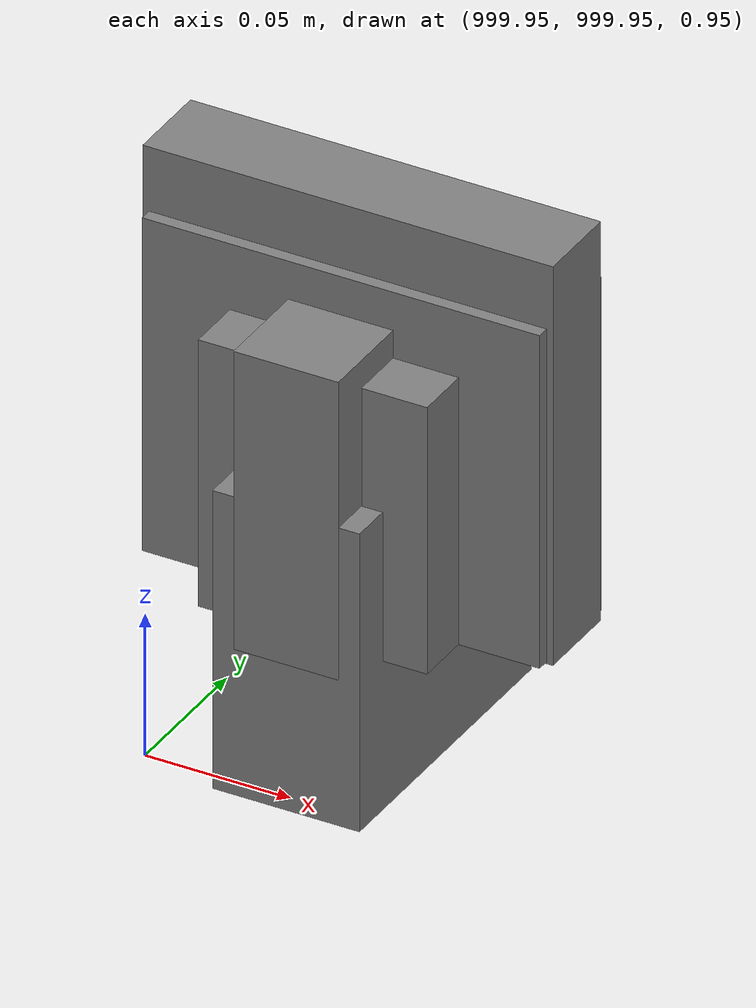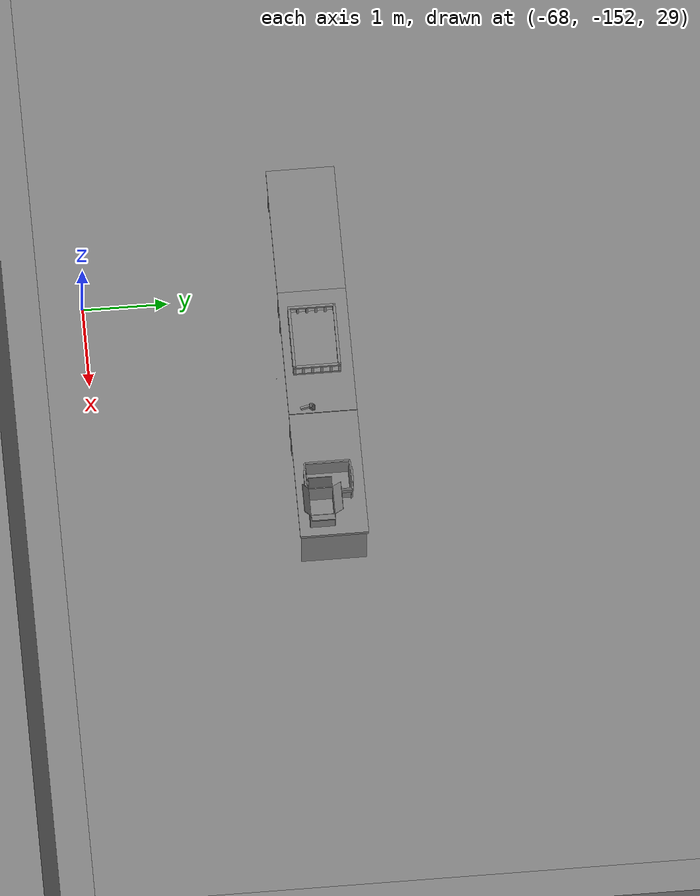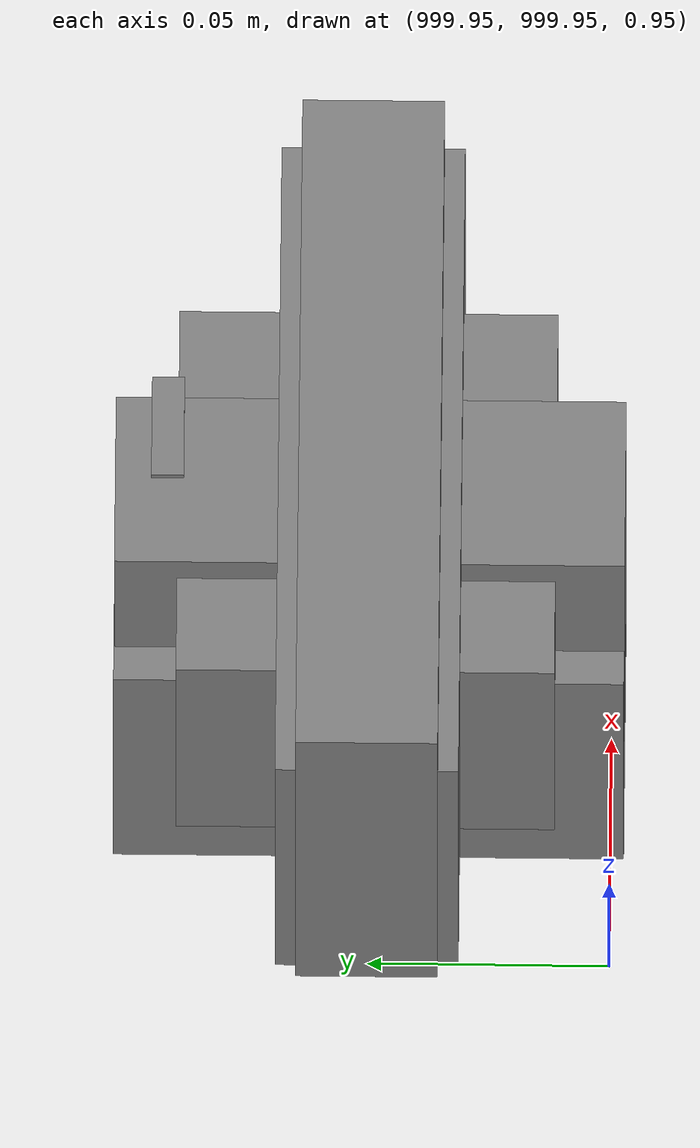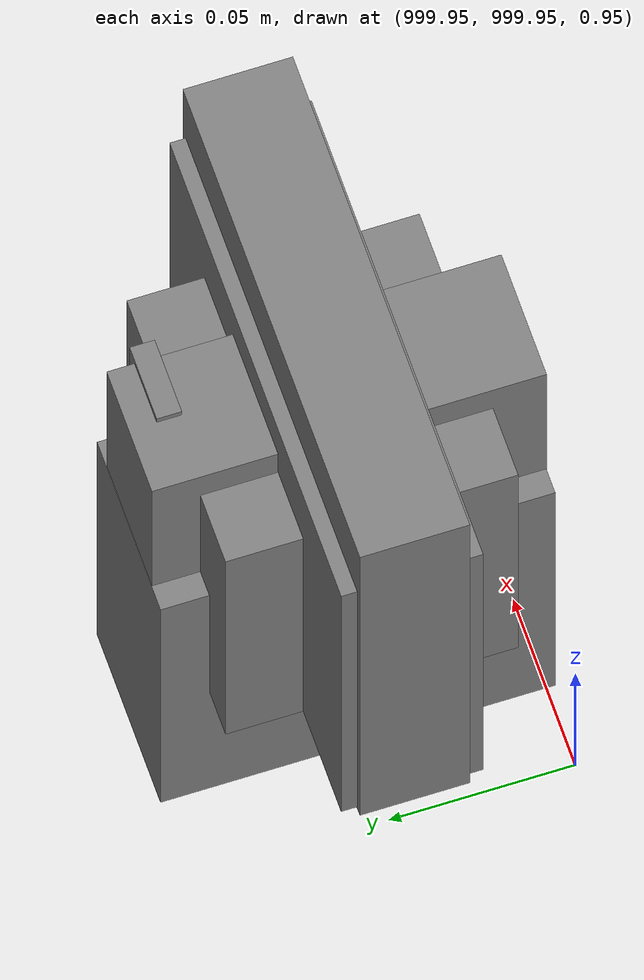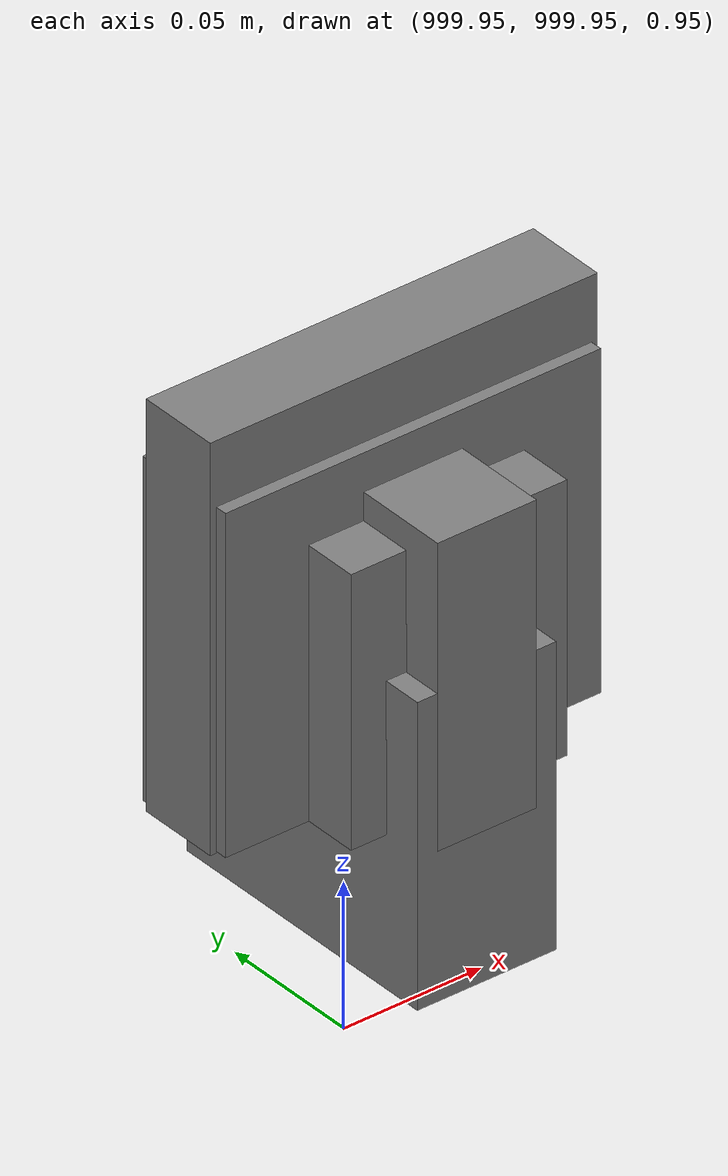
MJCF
<mujoco>
    <option gravity="0.000000000 0.000000000 -9.810000420" timestep="0.0049999999" integrator="implicitfast" density="1.225" viscosity="1.8000001e-05" noslip_iterations="10" iterations="100" sdf_iterations="50">
        <flag multiccd="disable"/>
    </option>
    <size memory="1000M"/>
    <compiler coordinate="local"/>
    <worldbody>
        <light cutoff="30" pos="0 1 1" dir="0 -1 -2"/>
        <light cutoff="30" pos="0 -1 1" dir="0 1 -2"/>
        <body pos="-64.866622925 -149.383972168 30.183746338" euler="89.999984741 89.999946594 0.000000000" name="openloong_gripper_2f85_fix_base_usda_bluebox_01">
            <geom contype="1" conaffinity="1" density="1000" type="box" material="" rgba="0.500000000 0.500000000 0.500000000 1.000000000" solimp="0.899999976 0.949999988 0.001000000" friction="1.000000000 0.005000000 0.000100000" solref="0.020000000 1.000000000" margin="0" condim="3" group="0" pos="0.276580811 0.187225342 0.000068665" quat="0.707106948 0.000077471 0.707106352 0.000077486" size="0.100000001 0.057999998 0.010000000" name="openloong_gripper_2f85_fix_base_usda_geom_3B364A6D_93D7_43E5_B2A7_459787B37897"/>
            <geom contype="1" conaffinity="1" density="1000" type="box" material="" rgba="0.500000000 0.500000000 0.500000000 1.000000000" solimp="0.899999976 0.949999988 0.001000000" friction="1.000000000 0.005000000 0.000100000" solref="0.020000000 1.000000000" margin="0" condim="3" group="0" pos="0.000000000 0.002883911 0.000000000" quat="0.999999881 0.000000000 0.000000000 0.000000000" size="0.254000008 0.003000000 0.172000006" name="openloong_gripper_2f85_fix_base_usda_geom_4A8D0DFA_C190_409C_8DB4_B45A7F4E68F4"/>
            <geom contype="1" conaffinity="1" density="1000" type="box" material="" rgba="0.500000000 0.500000000 0.500000000 1.000000000" solimp="0.899999976 0.949999988 0.001000000" friction="1.000000000 0.005000000 0.000100000" solref="0.020000000 1.000000000" margin="0" condim="3" group="0" pos="0.000000000 0.124874115 0.173484802" quat="0.999796331 0.020176515 -0.000000015 0.000000030" size="0.259999990 0.119999997 0.007000000" name="openloong_gripper_2f85_fix_base_usda_geom_BC8C7885_449E_40DF_BA82_98EE65857CF9"/>
            <geom contype="1" conaffinity="1" density="1000" type="box" material="" rgba="0.500000000 0.500000000 0.500000000 1.000000000" solimp="0.899999976 0.949999988 0.001000000" friction="1.000000000 0.005000000 0.000100000" solref="0.020000000 1.000000000" margin="0" condim="3" group="0" pos="0.000000000 0.124874115 -0.173469543" quat="0.999796331 -0.020176545 -0.000000015 0.000000000" size="0.259999990 0.119999997 0.007000000" name="openloong_gripper_2f85_fix_base_usda_geom_800AD2F8_5B14_4D59_80F6_16057E70CFB3"/>
            <geom contype="1" conaffinity="1" density="1000" type="box" material="" rgba="0.500000000 0.500000000 0.500000000 1.000000000" solimp="0.899999976 0.949999988 0.001000000" friction="1.000000000 0.005000000 0.000100000" solref="0.020000000 1.000000000" margin="0" condim="3" group="0" pos="0.000000000 0.214008331 0.188980103" quat="0.999912977 0.013176724 0.000000015 0.000000000" size="0.259999990 0.029999999 0.012500000" name="openloong_gripper_2f85_fix_base_usda_geom_0B62201D_EF9C_4452_8EA2_56754DB93EBA"/>
            <geom contype="1" conaffinity="1" density="1000" type="box" material="" rgba="0.500000000 0.500000000 0.500000000 1.000000000" solimp="0.899999976 0.949999988 0.001000000" friction="1.000000000 0.005000000 0.000100000" solref="0.020000000 1.000000000" margin="0" condim="3" group="0" pos="-0.258361816 0.125289917 0.001876831" quat="0.702796936 -0.020792112 0.710783124 0.020769298" size="0.189999998 0.119999997 0.009000000" name="openloong_gripper_2f85_fix_base_usda_geom_D518DC57_4E17_4AD7_9B93_561C17AA27AC"/>
            <geom contype="1" conaffinity="1" density="1000" type="box" material="" rgba="0.500000000 0.500000000 0.500000000 1.000000000" solimp="0.899999976 0.949999988 0.001000000" friction="1.000000000 0.005000000 0.000100000" solref="0.020000000 1.000000000" margin="0" condim="3" group="0" pos="0.000000000 0.214008331 -0.188980103" quat="0.999912977 -0.013176769 0.000000030 0.000000015" size="0.259999990 0.029999999 0.012500000" name="openloong_gripper_2f85_fix_base_usda_geom_E7599B4E_CC26_4C7E_BE34_194E0705C6C3"/>
            <geom contype="1" conaffinity="1" density="1000" type="box" material="" rgba="0.500000000 0.500000000 0.500000000 1.000000000" solimp="0.899999976 0.949999988 0.001000000" friction="1.000000000 0.005000000 0.000100000" solref="0.020000000 1.000000000" margin="0" condim="3" group="0" pos="-0.276611328 0.187225342 0.000068665" quat="0.707106650 0.000077441 0.707106709 0.000077456" size="0.100000001 0.057999998 0.010000000" name="openloong_gripper_2f85_fix_base_usda_geom_C85EE9C7_6014_4BCB_9E04_3B0F40B0FBBA"/>
            <geom contype="1" conaffinity="1" density="1000" type="box" material="" rgba="0.500000000 0.500000000 0.500000000 1.000000000" solimp="0.899999976 0.949999988 0.001000000" friction="1.000000000 0.005000000 0.000100000" solref="0.020000000 1.000000000" margin="0" condim="3" group="0" pos="0.258331299 0.125289917 0.001876831" quat="0.702851415 0.018856421 0.710823774 -0.019329369" size="0.189999998 0.119999997 0.009000000" name="openloong_gripper_2f85_fix_base_usda_geom_EC87CE32_CA38_4C1A_A0A6_7FE92F64A280"/>
            <freejoint name="openloong_gripper_2f85_fix_base_usda_bluebox_01_joint"/>
            <site size="0.005000000 0.005000000 0.005000000" rgba="0.500000000 0.500000000 0.500000000 1.000000000" pos="0.000000000 0.000000000 0.000000000" quat="0.999961913 0.008726534 0.000000000 0.000000000" group="0" type="sphere" name="openloong_gripper_2f85_fix_base_usda_bluebox_01site"/>
        </body>
        <body pos="-64.496299744 -149.491867065 30.235729218" euler="0.000000000 0.000000000 89.999946594" name="openloong_gripper_2f85_fix_base_usda_cardboardbox_01">
            <geom contype="1" conaffinity="1" density="1000" type="box" material="" rgba="0.500000000 0.500000000 0.500000000 1.000000000" solimp="0.899999976 0.949999988 0.001000000" friction="1.000000000 0.005000000 0.000100000" solref="0.020000000 1.000000000" margin="0" condim="3" group="0" pos="-0.003166199 -0.004086494 0.005052090" quat="1.000000000 0.000000000 0.000000000 0.000000000" size="0.142499998 0.177500010 0.005000000" name="openloong_gripper_2f85_fix_base_usda_geom_C77EFB56_B12B_4125_8B09_7EC35BC41BD8"/>
            <geom contype="1" conaffinity="1" density="1000" type="box" material="" rgba="0.500000000 0.500000000 0.500000000 1.000000000" solimp="0.899999976 0.949999988 0.001000000" friction="1.000000000 0.005000000 0.000100000" solref="0.020000000 1.000000000" margin="0" condim="3" group="0" pos="-0.003166199 0.170316696 0.150570869" quat="1.000000000 0.000000000 0.000000000 0.000000000" size="0.142499998 0.005000000 0.149999991" name="openloong_gripper_2f85_fix_base_usda_geom_6D2EB7D0_F285_451A_8C4B_5B744DC59CA9"/>
            <geom contype="1" conaffinity="1" density="1000" type="box" material="" rgba="0.500000000 0.500000000 0.500000000 1.000000000" solimp="0.899999976 0.949999988 0.001000000" friction="1.000000000 0.005000000 0.000100000" solref="0.020000000 1.000000000" margin="0" condim="3" group="0" pos="-0.147399902 -0.005307198 0.150570869" quat="1.000000000 0.000000000 0.000000000 0.000000000" size="0.005000000 0.177500010 0.149999991" name="openloong_gripper_2f85_fix_base_usda_geom_8D465323_BD19_4C33_BF05_4ADAEF75F3DA"/>
            <geom contype="1" conaffinity="1" density="1000" type="box" material="" rgba="0.500000000 0.500000000 0.500000000 1.000000000" solimp="0.899999976 0.949999988 0.001000000" friction="1.000000000 0.005000000 0.000100000" solref="0.020000000 1.000000000" margin="0" condim="3" group="0" pos="0.140275955 -0.005307198 0.150570869" quat="1.000000000 0.000000000 0.000000000 0.000000000" size="0.005000000 0.177500010 0.149999991" name="openloong_gripper_2f85_fix_base_usda_geom_569F7363_AE9D_4B56_88B2_2777130AB39B"/>
            <geom contype="1" conaffinity="1" density="1000" type="box" material="" rgba="0.500000000 0.500000000 0.500000000 1.000000000" solimp="0.899999976 0.949999988 0.001000000" friction="1.000000000 0.005000000 0.000100000" solref="0.020000000 1.000000000" margin="0" condim="3" group="0" pos="-0.003166199 -0.181550980 0.150570869" quat="1.000000000 0.000000000 0.000000000 0.000000000" size="0.142499998 0.005000000 0.149999991" name="openloong_gripper_2f85_fix_base_usda_geom_59E5CE06_6315_4C73_A04C_9929F5D9BFBF"/>
            <freejoint name="openloong_gripper_2f85_fix_base_usda_cardboardbox_01_joint"/>
            <site size="0.005000000 0.005000000 0.005000000" rgba="0.500000000 0.500000000 0.500000000 1.000000000" pos="0.000000000 0.000000000 0.000000000" quat="0.999961913 0.008726535 0.000000000 0.000000000" group="0" type="sphere" name="openloong_gripper_2f85_fix_base_usda_site_C888B308_40F0_453B_A2A1_E48F0241AF60"/>
            <body pos="0.139160156 -0.004048347 0.301930904" euler="-179.999954224 49.383502960 179.999954224" name="openloong_gripper_2f85_fix_base_usda_A1_006">
                <geom contype="1" conaffinity="1" density="1000" type="box" material="" rgba="0.500000000 0.500000000 0.500000000 1.000000000" solimp="0.899999976 0.949999988 0.001000000" friction="1.000000000 0.005000000 0.000100000" solref="0.020000000 1.000000000" margin="0" condim="3" group="0" pos="-0.071587563 0.000009537 0.001745224" quat="0.999999881 0.000000000 0.000000000 0.000000000" size="0.071249999 0.179999992 0.002500000" name="openloong_gripper_2f85_fix_base_usda_geom_A8282098_8127_467B_A7FB_E0460EA473CF"/>
                <joint armature="0" stiffness="0.07" damping="0.0099999998" axis="0.000000 1.000000 0.000000" type="hinge" name="openloong_gripper_2f85_fix_base_usda_A1_006"/>
            </body>
            <body pos="-0.145902634 -0.004086494 0.301938057" euler="-180.000000000 -60.000011444 -180.000000000" name="openloong_gripper_2f85_fix_base_usda_A2_006">
                <geom contype="1" conaffinity="1" density="1000" type="box" material="" rgba="0.500000000 0.500000000 0.500000000 1.000000000" solimp="0.899999976 0.949999988 0.001000000" friction="1.000000000 0.005000000 0.000100000" solref="0.020000000 1.000000000" margin="0" condim="3" group="0" pos="0.071268082 0.000009537 0.002717972" quat="0.000002921 0.000000000 -0.000000030 0.999999881" size="0.071249999 0.179999992 0.002500000" name="openloong_gripper_2f85_fix_base_usda_geom_0BC8E6BA_7A12_4EDE_A16E_0622A88B2AC8"/>
                <joint armature="0" stiffness="0.07" damping="0.0099999998" axis="0.000000 1.000000 0.000000" type="hinge" name="openloong_gripper_2f85_fix_base_usda_A2_006"/>
            </body>
            <body pos="-0.003385544 0.175991058 0.301930904" euler="-125.858116150 -0.000004561 0.000002331" name="openloong_gripper_2f85_fix_base_usda_B2_006">
                <geom contype="1" conaffinity="1" density="1000" type="box" material="" rgba="0.500000000 0.500000000 0.500000000 1.000000000" solimp="0.899999976 0.949999988 0.001000000" friction="1.000000000 0.005000000 0.000100000" solref="0.020000000 1.000000000" margin="0" condim="3" group="0" pos="0.000009537 -0.070939064 -0.002470016" quat="0.999614120 0.027776197 -0.000000015 0.000000030" size="0.137500003 0.064999998 0.005000000" name="openloong_gripper_2f85_fix_base_usda_geom_17A8A96F_7A4F_4B03_94D9_517B6D42C479"/>
                <joint armature="0" stiffness="0.07" damping="0.0099999998" axis="1.000000 0.000000 0.000000" type="hinge" name="openloong_gripper_2f85_fix_base_usda_B2_006"/>
            </body>
            <body pos="-0.003385544 -0.184140205 0.301938057" euler="147.805557251 0.000000000 0.000000000" name="openloong_gripper_2f85_fix_base_usda_B1_006">
                <geom contype="1" conaffinity="1" density="1000" type="box" material="" rgba="0.500000000 0.500000000 0.500000000 1.000000000" solimp="0.899999976 0.949999988 0.001000000" friction="1.000000000 0.005000000 0.000100000" solref="0.020000000 1.000000000" margin="0" condim="3" group="0" pos="-0.000028610 0.070202351 -0.002703667" quat="0.999614179 -0.027776167 0.000000000 0.000000000" size="0.137500003 0.064999998 0.005000000" name="openloong_gripper_2f85_fix_base_usda_geom_D13B3588_4EE7_421C_B53B_A78002F0B1FD"/>
                <joint armature="0" stiffness="0.07" damping="0.0099999998" axis="1.000000 0.000000 0.000000" type="hinge" name="openloong_gripper_2f85_fix_base_usda_B1_006"/>
            </body>
        </body>
        <body pos="-65.882858276 -149.481979370 30.229999542" euler="-64.487716675 0.000000000 0.000000000" name="openloong_gripper_2f85_fix_base_usda_Barcode">
            <geom contype="1" conaffinity="1" density="1000" type="box" material="" rgba="0.500000000 0.500000000 0.500000000 1.000000000" solimp="0.899999976 0.949999988 0.001000000" friction="1.000000000 0.005000000 0.000100000" solref="0.020000000 1.000000000" margin="0" condim="3" group="0" pos="0.000000000 0.013038635 0.001419067" quat="0.000000000 0.000000000 0.000000000 1.000000119" size="0.034000002 0.010000000 0.017999999" name="openloong_gripper_2f85_fix_base_usda_geom_146C0DA7_BDC1_4676_82F2_D6169BC1D6F1"/>
            <geom contype="1" conaffinity="1" density="1000" type="box" material="" rgba="0.500000000 0.500000000 0.500000000 1.000000000" solimp="0.899999976 0.949999988 0.001000000" friction="1.000000000 0.005000000 0.000100000" solref="0.020000000 1.000000000" margin="0" condim="3" group="0" pos="0.000000000 -0.035301208 -0.007095337" quat="0.000000000 0.000000000 -0.043619365 0.999048233" size="0.028999999 0.010000000 0.020000000" name="openloong_gripper_2f85_fix_base_usda_geom_B0887383_BA42_4F6A_ACD9_9B54AD6BEEBD"/>
            <geom contype="1" conaffinity="1" density="1000" type="box" material="" rgba="0.500000000 0.500000000 0.500000000 1.000000000" solimp="0.899999976 0.949999988 0.001000000" friction="1.000000000 0.005000000 0.000100000" solref="0.020000000 1.000000000" margin="0" condim="3" group="0" pos="0.000000000 -0.043411255 -0.011749268" quat="0.922262907 0.386563420 0.000000000 0.000000000" size="0.026000001 0.010000000 0.020000000" name="openloong_gripper_2f85_fix_base_usda_geom_89237DC7_7A48_4899_AC3D_38BCB1BC272B"/>
            <geom contype="1" conaffinity="1" density="1000" type="box" material="" rgba="0.500000000 0.500000000 0.500000000 1.000000000" solimp="0.899999976 0.949999988 0.001000000" friction="1.000000000 0.005000000 0.000100000" solref="0.020000000 1.000000000" margin="0" condim="3" group="0" pos="0.000000000 -0.016967773 -0.031860352" quat="0.000000000 0.000000000 0.000000000 1.000000119" size="0.008000000 0.010000000 0.013000000" name="openloong_gripper_2f85_fix_base_usda_geom_93BE980B_8850_4257_9D65_B2604160E2DA"/>
            <geom contype="1" conaffinity="1" density="1000" type="box" material="" rgba="0.500000000 0.500000000 0.500000000 1.000000000" solimp="0.899999976 0.949999988 0.001000000" friction="1.000000000 0.005000000 0.000100000" solref="0.020000000 1.000000000" margin="0" condim="3" group="0" pos="0.000000000 -0.001869202 0.000312805" quat="0.953716993 0.300705761 0.000000000 0.000000000" size="0.032000002 0.010000000 0.018999999" name="openloong_gripper_2f85_fix_base_usda_geom_90B73FB0_D2F7_424E_93A0_2B9BA6D83698"/>
            <geom contype="1" conaffinity="1" density="1000" type="box" material="" rgba="0.500000000 0.500000000 0.500000000 1.000000000" solimp="0.899999976 0.949999988 0.001000000" friction="1.000000000 0.005000000 0.000100000" solref="0.020000000 1.000000000" margin="0" condim="3" group="0" pos="0.000000000 -0.019531250 -0.003173828" quat="0.953716993 0.300705761 0.000000000 0.000000000" size="0.030999999 0.010000000 0.020000000" name="openloong_gripper_2f85_fix_base_usda_geom_716E5F4D_4820_4A7A_8C15_894EA9F7A811"/>
            <geom contype="1" conaffinity="1" density="1000" type="box" material="" rgba="0.500000000 0.500000000 0.500000000 1.000000000" solimp="0.899999976 0.949999988 0.001000000" friction="1.000000000 0.005000000 0.000100000" solref="0.020000000 1.000000000" margin="0" condim="3" group="0" pos="0.000000000 -0.035301208 -0.007095337" quat="0.953716993 0.300705761 0.000000000 0.000000000" size="0.028999999 0.010000000 0.020000000" name="openloong_gripper_2f85_fix_base_usda_geom_14835DB2_1658_4838_9199_8259035ACDE7"/>
            <geom contype="1" conaffinity="1" density="1000" type="box" material="" rgba="0.500000000 0.500000000 0.500000000 1.000000000" solimp="0.899999976 0.949999988 0.001000000" friction="1.000000000 0.005000000 0.000100000" solref="0.020000000 1.000000000" margin="0" condim="3" group="0" pos="0.000000000 -0.042617798 -0.071121216" quat="0.000000000 0.000000000 0.000000000 1.000000119" size="0.013000000 0.021000000 0.059999999" name="openloong_gripper_2f85_fix_base_usda_geom_178ECDE0_760E_4B6E_85CC_7FB56B8211E8"/>
            <freejoint name="openloong_gripper_2f85_fix_base_usda_Barcode_joint"/>
            <site size="0.005000000 0.005000000 0.005000000" rgba="0.500000000 0.500000000 0.500000000 1.000000000" pos="0.000000000 0.000000000 0.000000000" quat="1.000000000 0.000000000 0.000000000 0.000000000" group="0" type="sphere" name="openloong_gripper_2f85_fix_base_usda_Barcode_site"/>
        </body>
        <body pos="-66.745018005 -149.392349243 30.184000015" euler="0.000000000 0.000000000 89.999946594" name="[22329757093671]_Basket_01">
            <geom contype="1" conaffinity="1" density="1000" type="box" material="" rgba="0.500000000 0.500000000 0.500000000 1.000000000" solimp="0.899999976 0.949999988 0.001000000" friction="1.000000000 0.005000000 0.000100000" solref="0.020000000 1.000000000" margin="0" condim="3" group="0" pos="-0.052425385 0.389207840 0.089787483" quat="0.707107008 0.000000000 0.000000000 0.707106411" size="0.014249999 0.014249999 0.059999999" name="[22329757093671]_geom_4F223684_4BC6_4680_988A_ABA57529D29E"/>
            <geom contype="1" conaffinity="1" density="1000" type="box" material="" rgba="0.500000000 0.500000000 0.500000000 1.000000000" solimp="0.899999976 0.949999988 0.001000000" friction="1.000000000 0.005000000 0.000100000" solref="0.020000000 1.000000000" margin="0" condim="3" group="0" pos="0.264015198 -0.133043289 0.089787483" quat="0.707107008 0.000000000 0.000000000 0.707106411" size="0.014249999 0.014249999 0.059999999" name="[22329757093671]_geom_AC8EDF6A_C618_4D81_BCF8_6DCB95A929C4"/>
            <geom contype="1" conaffinity="1" density="1000" type="box" material="" rgba="0.500000000 0.500000000 0.500000000 1.000000000" solimp="0.899999976 0.949999988 0.001000000" friction="1.000000000 0.005000000 0.000100000" solref="0.020000000 1.000000000" margin="0" condim="3" group="0" pos="-0.264015198 -0.265548706 0.089793205" quat="0.707107008 0.000000000 0.000000000 0.707106411" size="0.014249999 0.014249999 0.059999999" name="[22329757093671]_geom_2AEDB0DE_785A_4BC5_B290_B0CFD1C327D0"/>
            <geom contype="1" conaffinity="1" density="1000" type="box" material="" rgba="0.500000000 0.500000000 0.500000000 1.000000000" solimp="0.899999976 0.949999988 0.001000000" friction="1.000000000 0.005000000 0.000100000" solref="0.020000000 1.000000000" margin="0" condim="3" group="0" pos="-0.160263062 -0.389322281 0.089793205" quat="0.707107008 0.000000000 0.000000000 0.707106411" size="0.014249999 0.014249999 0.059999999" name="[22329757093671]_geom_F99FD198_CF84_472D_81A5_E0BEF0510B70"/>
            <geom contype="1" conaffinity="1" density="1000" type="box" material="" rgba="0.500000000 0.500000000 0.500000000 1.000000000" solimp="0.899999976 0.949999988 0.001000000" friction="1.000000000 0.005000000 0.000100000" solref="0.020000000 1.000000000" margin="0" condim="3" group="0" pos="0.162265778 -0.389322281 0.089787483" quat="0.707107008 0.000000000 0.000000000 0.707106411" size="0.014249999 0.014249999 0.059999999" name="[22329757093671]_geom_9E04F839_8A4B_41DB_813E_97B3F18EEC08"/>
            <geom contype="1" conaffinity="1" density="1000" type="box" material="" rgba="0.500000000 0.500000000 0.500000000 1.000000000" solimp="0.899999976 0.949999988 0.001000000" friction="1.000000000 0.005000000 0.000100000" solref="0.020000000 1.000000000" margin="0" condim="3" group="0" pos="0.264015198 0.389207840 0.089787483" quat="0.707107008 0.000000000 0.000000000 0.707106411" size="0.014249999 0.014249999 0.059999999" name="[22329757093671]_geom_9BFC561F_1D9B_42CD_95A6_6F02832A4D9B"/>
            <geom contype="1" conaffinity="1" density="1000" type="box" material="" rgba="0.500000000 0.500000000 0.500000000 1.000000000" solimp="0.899999976 0.949999988 0.001000000" friction="1.000000000 0.005000000 0.000100000" solref="0.020000000 1.000000000" margin="0" condim="3" group="0" pos="-0.264015198 -0.133043289 0.089793205" quat="0.707107008 0.000000000 0.000000000 0.707106411" size="0.014249999 0.014249999 0.059999999" name="[22329757093671]_geom_84B26B38_1473_4C07_AAA0_A05373ED7103"/>
            <geom contype="1" conaffinity="1" density="1000" type="box" material="" rgba="0.500000000 0.500000000 0.500000000 1.000000000" solimp="0.899999976 0.949999988 0.001000000" friction="1.000000000 0.005000000 0.000100000" solref="0.020000000 1.000000000" margin="0" condim="3" group="0" pos="-0.264026642 0.269256592 0.089793205" quat="0.707107008 0.000000000 0.000000000 0.707106411" size="0.014249999 0.014249999 0.059999999" name="[22329757093671]_geom_2E4A97DA_1549_4F4E_B461_237AF1050EDD"/>
            <geom contype="1" conaffinity="1" density="1000" type="box" material="" rgba="0.500000000 0.500000000 0.500000000 1.000000000" solimp="0.899999976 0.949999988 0.001000000" friction="1.000000000 0.005000000 0.000100000" solref="0.020000000 1.000000000" margin="0" condim="3" group="0" pos="0.054462433 0.389207840 0.089787483" quat="0.707107008 0.000000000 0.000000000 0.707106411" size="0.014249999 0.014249999 0.059999999" name="[22329757093671]_geom_34E91BA5_3419_4D93_9681_C0CE7582AEC8"/>
            <geom contype="1" conaffinity="1" density="1000" type="box" material="" rgba="0.500000000 0.500000000 0.500000000 1.000000000" solimp="0.899999976 0.949999988 0.001000000" friction="1.000000000 0.005000000 0.000100000" solref="0.020000000 1.000000000" margin="0" condim="3" group="0" pos="0.054462433 -0.389322281 0.089787483" quat="0.707107008 0.000000000 0.000000000 0.707106411" size="0.014249999 0.014249999 0.059999999" name="[22329757093671]_geom_ACF89C80_840F_4474_9E05_6B7595DADF1D"/>
            <geom contype="1" conaffinity="1" density="1000" type="box" material="" rgba="0.500000000 0.500000000 0.500000000 1.000000000" solimp="0.899999976 0.949999988 0.001000000" friction="1.000000000 0.005000000 0.000100000" solref="0.020000000 1.000000000" margin="0" condim="3" group="0" pos="0.264015198 0.269256592 0.089793205" quat="0.707107008 0.000000000 0.000000000 0.707106411" size="0.014249999 0.014249999 0.059999999" name="[22329757093671]_geom_23AE6B86_1DAA_41B9_9D90_43E76DADD6E9"/>
            <geom contype="1" conaffinity="1" density="1000" type="box" material="" rgba="0.500000000 0.500000000 0.500000000 1.000000000" solimp="0.899999976 0.949999988 0.001000000" friction="1.000000000 0.005000000 0.000100000" solref="0.020000000 1.000000000" margin="0" condim="3" group="0" pos="0.264015198 -0.389322281 0.089787483" quat="0.707107008 0.000000000 0.000000000 0.707106411" size="0.014249999 0.014249999 0.059999999" name="[22329757093671]_geom_B98C0E12_533E_4F8D_9F08_866E96678716"/>
            <geom contype="1" conaffinity="1" density="1000" type="box" material="" rgba="0.500000000 0.500000000 0.500000000 1.000000000" solimp="0.899999976 0.949999988 0.001000000" friction="1.000000000 0.005000000 0.000100000" solref="0.020000000 1.000000000" margin="0" condim="3" group="0" pos="0.000000000 0.000000000 0.015998840" quat="0.707107008 0.000000000 0.000000000 0.707106411" size="0.403499991 0.279000014 0.015750000" name="[22329757093671]_geom_187CBEC2_C8DF_4459_A465_8667A2E4CA05"/>
            <geom contype="1" conaffinity="1" density="1000" type="box" material="" rgba="0.500000000 0.500000000 0.500000000 1.000000000" solimp="0.899999976 0.949999988 0.001000000" friction="1.000000000 0.005000000 0.000100000" solref="0.020000000 1.000000000" margin="0" condim="3" group="0" pos="0.000000000 -0.389476776 0.163619041" quat="0.707107008 0.000000000 0.000000000 0.707106411" size="0.015000000 0.277500004 0.015750000" name="[22329757093671]_geom_AFCDC62D_594A_402E_8953_24C912476988"/>
            <geom contype="1" conaffinity="1" density="1000" type="box" material="" rgba="0.500000000 0.500000000 0.500000000 1.000000000" solimp="0.899999976 0.949999988 0.001000000" friction="1.000000000 0.005000000 0.000100000" solref="0.020000000 1.000000000" margin="0" condim="3" group="0" pos="0.162265778 0.389207840 0.089787483" quat="0.707107008 0.000000000 0.000000000 0.707106411" size="0.014249999 0.014249999 0.059999999" name="[22329757093671]_geom_81BAB3C0_1CCF_4086_8224_4D6C7A860464"/>
            <geom contype="1" conaffinity="1" density="1000" type="box" material="" rgba="0.500000000 0.500000000 0.500000000 1.000000000" solimp="0.899999976 0.949999988 0.001000000" friction="1.000000000 0.005000000 0.000100000" solref="0.020000000 1.000000000" margin="0" condim="3" group="0" pos="0.000000000 0.389471054 0.163619041" quat="0.707107008 0.000000000 0.000000000 0.707106411" size="0.015000000 0.277500004 0.015750000" name="[22329757093671]_geom_36305D93_F2D0_4574_B24E_B9C77EE0427C"/>
            <geom contype="1" conaffinity="1" density="1000" type="box" material="" rgba="0.500000000 0.500000000 0.500000000 1.000000000" solimp="0.899999976 0.949999988 0.001000000" friction="1.000000000 0.005000000 0.000100000" solref="0.020000000 1.000000000" margin="0" condim="3" group="0" pos="-0.263511658 0.000000000 0.163619041" quat="0.707107008 0.000000000 0.000000000 0.707106411" size="0.403499991 0.015000000 0.015750000" name="[22329757093671]_geom_D2BE722E_4536_461F_9172_1B2CF47F4CD1"/>
            <geom contype="1" conaffinity="1" density="1000" type="box" material="" rgba="0.500000000 0.500000000 0.500000000 1.000000000" solimp="0.899999976 0.949999988 0.001000000" friction="1.000000000 0.005000000 0.000100000" solref="0.020000000 1.000000000" margin="0" condim="3" group="0" pos="-0.264015198 0.141334534 0.089793205" quat="0.707107008 0.000000000 0.000000000 0.707106411" size="0.014249999 0.014249999 0.059999999" name="[22329757093671]_geom_FBADCFFC_E09B_4FE7_9DD0_B0823CFD249C"/>
            <geom contype="1" conaffinity="1" density="1000" type="box" material="" rgba="0.500000000 0.500000000 0.500000000 1.000000000" solimp="0.899999976 0.949999988 0.001000000" friction="1.000000000 0.005000000 0.000100000" solref="0.020000000 1.000000000" margin="0" condim="3" group="0" pos="0.264015198 -0.265548706 0.089787483" quat="0.707107008 0.000000000 0.000000000 0.707106411" size="0.014249999 0.014249999 0.059999999" name="[22329757093671]_geom_AF857274_9F11_4EC9_9783_C7C81FC5B8AA"/>
            <geom contype="1" conaffinity="1" density="1000" type="box" material="" rgba="0.500000000 0.500000000 0.500000000 1.000000000" solimp="0.899999976 0.949999988 0.001000000" friction="1.000000000 0.005000000 0.000100000" solref="0.020000000 1.000000000" margin="0" condim="3" group="0" pos="-0.160263062 0.389207840 0.089787483" quat="0.707107008 0.000000000 0.000000000 0.707106411" size="0.014249999 0.014249999 0.059999999" name="[22329757093671]_geom_2350D12F_AC94_4492_809C_A80D99CFD9DC"/>
            <geom contype="1" conaffinity="1" density="1000" type="box" material="" rgba="0.500000000 0.500000000 0.500000000 1.000000000" solimp="0.899999976 0.949999988 0.001000000" friction="1.000000000 0.005000000 0.000100000" solref="0.020000000 1.000000000" margin="0" condim="3" group="0" pos="-0.052425385 -0.389322281 0.089787483" quat="0.707107008 0.000000000 0.000000000 0.707106411" size="0.014249999 0.014249999 0.059999999" name="[22329757093671]_geom_AA1492D7_3A1D_43D4_90FE_4D84BE2D64CE"/>
            <geom contype="1" conaffinity="1" density="1000" type="box" material="" rgba="0.500000000 0.500000000 0.500000000 1.000000000" solimp="0.899999976 0.949999988 0.001000000" friction="1.000000000 0.005000000 0.000100000" solref="0.020000000 1.000000000" margin="0" condim="3" group="0" pos="-0.264026642 -0.389322281 0.089793205" quat="0.707107008 0.000000000 0.000000000 0.707106411" size="0.014249999 0.014249999 0.059999999" name="[22329757093671]_geom_D726AEE4_89B5_456C_B920_EC38ABBD3922"/>
            <geom contype="1" conaffinity="1" density="1000" type="box" material="" rgba="0.500000000 0.500000000 0.500000000 1.000000000" solimp="0.899999976 0.949999988 0.001000000" friction="1.000000000 0.005000000 0.000100000" solref="0.020000000 1.000000000" margin="0" condim="3" group="0" pos="0.264015198 0.141334534 0.089787483" quat="0.707107008 0.000000000 0.000000000 0.707106411" size="0.014249999 0.014249999 0.059999999" name="[22329757093671]_geom_1425B860_BD4F_49A5_B714_2B84EA574DA5"/>
            <geom contype="1" conaffinity="1" density="1000" type="box" material="" rgba="0.500000000 0.500000000 0.500000000 1.000000000" solimp="0.899999976 0.949999988 0.001000000" friction="1.000000000 0.005000000 0.000100000" solref="0.020000000 1.000000000" margin="0" condim="3" group="0" pos="-0.264015198 0.389207840 0.089793205" quat="0.707107008 0.000000000 0.000000000 0.707106411" size="0.014249999 0.014249999 0.059999999" name="[22329757093671]_geom_1A2A1DBA_2527_427D_BF94_62A30B7050E0"/>
            <geom contype="1" conaffinity="1" density="1000" type="box" material="" rgba="0.500000000 0.500000000 0.500000000 1.000000000" solimp="0.899999976 0.949999988 0.001000000" friction="1.000000000 0.005000000 0.000100000" solref="0.020000000 1.000000000" margin="0" condim="3" group="0" pos="0.264015198 0.004480362 0.089787483" quat="0.707107008 0.000000000 0.000000000 0.707106411" size="0.014249999 0.014249999 0.059999999" name="[22329757093671]_geom_9D371F04_2A4F_4A1E_AA51_6949D79873CD"/>
            <geom contype="1" conaffinity="1" density="1000" type="box" material="" rgba="0.500000000 0.500000000 0.500000000 1.000000000" solimp="0.899999976 0.949999988 0.001000000" friction="1.000000000 0.005000000 0.000100000" solref="0.020000000 1.000000000" margin="0" condim="3" group="0" pos="0.263694763 -0.000011444 0.163619041" quat="0.707107008 0.000000000 0.000000000 0.707106411" size="0.403499991 0.015000000 0.015750000" name="[22329757093671]_geom_A6AE3AA5_FFFD_487B_9863_E14716D56BCA"/>
            <geom contype="1" conaffinity="1" density="1000" type="box" material="" rgba="0.500000000 0.500000000 0.500000000 1.000000000" solimp="0.899999976 0.949999988 0.001000000" friction="1.000000000 0.005000000 0.000100000" solref="0.020000000 1.000000000" margin="0" condim="3" group="0" pos="-0.264015198 0.004480362 0.089793205" quat="0.707107008 0.000000000 0.000000000 0.707106411" size="0.014249999 0.014249999 0.059999999" name="[22329757093671]_geom_C9EF2C58_2185_4D09_8DF0_2DF48F25813D"/>
            <freejoint name="[22329757093671]_joint_C62E84BE_F215_493F_AC8D_CAA4D7DD3C62"/>
        </body>
        <body pos="0.000000000 0.000000000 0.000000000" euler="0.000000000 0.000000000 0.000000000" name="Static Objects_Static Objects">
            <geom contype="1" conaffinity="1" density="1000" type="box" material="" rgba="0.500000000 0.500000000 0.500000000 1.000000000" solimp="0.899999976 0.949999988 0.001000000" friction="1.000000000 0.005000000 0.000100000" solref="0.020000000 1.000000000" margin="0" condim="3" group="0" pos="-67.544113159 -149.365814209 29.727830887" quat="0.500000417 0.499999970 0.499999553 0.499999970" size="0.381000012 0.319999993 0.041000001" name="Static Objects_geom_9913C507_CB5B_4849_897E_5C6B2B3D12F2"/>
            <geom contype="1" conaffinity="1" density="1000" type="box" material="" rgba="0.500000000 0.500000000 0.500000000 1.000000000" solimp="0.899999976 0.949999988 0.001000000" friction="1.000000000 0.005000000 0.000100000" solref="0.020000000 1.000000000" margin="0" condim="3" group="0" pos="-68.239501953 -149.365814209 30.086868286" quat="0.500000417 0.499999970 0.499999553 0.499999970" size="0.370999992 0.039500002 0.745000005" name="Static Objects_geom_A33622B4_B150_4A11_9504_B7F6D24FBA30"/>
            <geom contype="1" conaffinity="1" density="1000" type="box" material="" rgba="0.500000000 0.500000000 0.500000000 1.000000000" solimp="0.899999976 0.949999988 0.001000000" friction="1.000000000 0.005000000 0.000100000" solref="0.020000000 1.000000000" margin="0" condim="3" group="0" pos="-68.239501953 -149.365814209 30.147235870" quat="0.500000417 0.499999970 0.499999553 0.499999970" size="0.400000006 0.022000000 0.800000012" name="Static Objects_geom_368ABEBF_2438_495D_B300_FF4728C50A86"/>
            <geom contype="1" conaffinity="1" density="1000" type="box" material="" rgba="0.500000000 0.500000000 0.500000000 1.000000000" solimp="0.899999976 0.949999988 0.001000000" friction="1.000000000 0.005000000 0.000100000" solref="0.020000000 1.000000000" margin="0" condim="3" group="0" pos="-68.934890747 -149.365814209 29.727830887" quat="0.500000417 0.499999970 0.499999553 0.499999970" size="0.381000012 0.319999993 0.041000001" name="Static Objects_geom_10EE5108_E452_4AC4_9275_D1D0E1D85A65"/>
            <geom contype="1" conaffinity="1" density="1000" type="box" material="" rgba="0.500000000 0.500000000 0.500000000 1.000000000" solimp="0.899999976 0.949999988 0.001000000" friction="1.000000000 0.005000000 0.000100000" solref="0.020000000 1.000000000" margin="0" condim="3" group="0" pos="-68.239501953 -149.365814209 29.561563492" quat="0.500000417 0.499999970 0.499999553 0.499999970" size="0.020000000 0.022000000 0.660000026" name="Static Objects_geom_4E33DD52_B59A_42CA_AE5C_3FB2FFC84B5F"/>
            <geom contype="1" conaffinity="1" density="1000" type="box" material="" rgba="0.500000000 0.500000000 0.500000000 1.000000000" solimp="0.899999976 0.949999988 0.001000000" friction="1.000000000 0.005000000 0.000100000" solref="0.020000000 1.000000000" margin="0" condim="3" group="0" pos="-65.945671082 -149.365814209 29.727830887" quat="0.500000417 0.499999970 0.499999553 0.499999970" size="0.381000012 0.319999993 0.041000001" name="Static Objects_geom_7243C9C0_2DFB_49F7_9DD4_DD0E72C5C5BB"/>
            <geom contype="1" conaffinity="1" density="1000" type="box" material="" rgba="0.500000000 0.500000000 0.500000000 1.000000000" solimp="0.899999976 0.949999988 0.001000000" friction="1.000000000 0.005000000 0.000100000" solref="0.020000000 1.000000000" margin="0" condim="3" group="0" pos="-66.641059875 -149.365814209 30.086868286" quat="0.500000417 0.499999970 0.499999553 0.499999970" size="0.370999992 0.039500002 0.745000005" name="Static Objects_geom_6EEEEC97_9764_4AB2_B668_956641E190D7"/>
            <geom contype="1" conaffinity="1" density="1000" type="box" material="" rgba="0.500000000 0.500000000 0.500000000 1.000000000" solimp="0.899999976 0.949999988 0.001000000" friction="1.000000000 0.005000000 0.000100000" solref="0.020000000 1.000000000" margin="0" condim="3" group="0" pos="-66.641059875 -149.365814209 30.147235870" quat="0.500000417 0.499999970 0.499999553 0.499999970" size="0.400000006 0.022000000 0.800000012" name="Static Objects_geom_DCCAE061_743A_46E9_A100_CA474C487DA0"/>
            <geom contype="1" conaffinity="1" density="1000" type="box" material="" rgba="0.500000000 0.500000000 0.500000000 1.000000000" solimp="0.899999976 0.949999988 0.001000000" friction="1.000000000 0.005000000 0.000100000" solref="0.020000000 1.000000000" margin="0" condim="3" group="0" pos="-67.336448669 -149.365814209 29.727830887" quat="0.500000417 0.499999970 0.499999553 0.499999970" size="0.381000012 0.319999993 0.041000001" name="Static Objects_geom_4A8AA602_E8CA_48CE_82FB_9DF06FE01ADD"/>
            <geom contype="1" conaffinity="1" density="1000" type="box" material="" rgba="0.500000000 0.500000000 0.500000000 1.000000000" solimp="0.899999976 0.949999988 0.001000000" friction="1.000000000 0.005000000 0.000100000" solref="0.020000000 1.000000000" margin="0" condim="3" group="0" pos="-66.641059875 -149.365814209 29.561563492" quat="0.500000417 0.499999970 0.499999553 0.499999970" size="0.020000000 0.022000000 0.660000026" name="Static Objects_geom_6874B198_8A16_45CC_B537_71862B3DEFAD"/>
            <geom contype="1" conaffinity="1" density="1000" type="box" material="" rgba="0.500000000 0.500000000 0.500000000 1.000000000" solimp="0.899999976 0.949999988 0.001000000" friction="1.000000000 0.005000000 0.000100000" solref="0.020000000 1.000000000" margin="0" condim="3" group="0" pos="-64.338577271 -149.365814209 29.727830887" quat="0.500000417 0.499999970 0.499999553 0.499999970" size="0.381000012 0.319999993 0.041000001" name="Static Objects_geom_8A14AF0B_993F_4776_8AE0_043605CAA24A"/>
            <geom contype="1" conaffinity="1" density="1000" type="box" material="" rgba="0.500000000 0.500000000 0.500000000 1.000000000" solimp="0.899999976 0.949999988 0.001000000" friction="1.000000000 0.005000000 0.000100000" solref="0.020000000 1.000000000" margin="0" condim="3" group="0" pos="-65.033966064 -149.365814209 30.086868286" quat="0.500000417 0.499999970 0.499999553 0.499999970" size="0.370999992 0.039500002 0.745000005" name="Static Objects_geom_4FC769AA_D5FA_47CE_B49F_077684D162D1"/>
            <geom contype="1" conaffinity="1" density="1000" type="box" material="" rgba="0.500000000 0.500000000 0.500000000 1.000000000" solimp="0.899999976 0.949999988 0.001000000" friction="1.000000000 0.005000000 0.000100000" solref="0.020000000 1.000000000" margin="0" condim="3" group="0" pos="-65.033966064 -149.365814209 30.147235870" quat="0.500000417 0.499999970 0.499999553 0.499999970" size="0.400000006 0.022000000 0.800000012" name="Static Objects_geom_EEA0C8D1_1142_45B3_9D75_DFC1B488E3A6"/>
            <geom contype="1" conaffinity="1" density="1000" type="box" material="" rgba="0.500000000 0.500000000 0.500000000 1.000000000" solimp="0.899999976 0.949999988 0.001000000" friction="1.000000000 0.005000000 0.000100000" solref="0.020000000 1.000000000" margin="0" condim="3" group="0" pos="-65.729354858 -149.365814209 29.727830887" quat="0.500000417 0.499999970 0.499999553 0.499999970" size="0.381000012 0.319999993 0.041000001" name="Static Objects_geom_A03C6537_08EE_4319_82FB_49A1F0B69A57"/>
            <geom contype="1" conaffinity="1" density="1000" type="box" material="" rgba="0.500000000 0.500000000 0.500000000 1.000000000" solimp="0.899999976 0.949999988 0.001000000" friction="1.000000000 0.005000000 0.000100000" solref="0.020000000 1.000000000" margin="0" condim="3" group="0" pos="-65.033966064 -149.365814209 29.561563492" quat="0.500000417 0.499999970 0.499999553 0.499999970" size="0.020000000 0.022000000 0.660000026" name="Static Objects_geom_45362481_2915_4CBF_8637_1AD99D8CDAF1"/>
            <geom contype="1" conaffinity="1" density="1000" type="box" material="" rgba="0.500000000 0.500000000 0.500000000 1.000000000" solimp="0.899999976 0.949999988 0.001000000" friction="1.000000000 0.005000000 0.000100000" solref="0.020000000 1.000000000" margin="0" condim="3" group="0" pos="-61.754566193 -137.853729248 33.906845093" quat="0.707107067 0.000000000 0.000000000 0.707106471" size="0.759999990 0.759999990 4.500000000" name="Static Objects_geom_3260C881_663A_4A3C_9143_40197E061E77"/>
            <geom contype="1" conaffinity="1" density="1000" type="box" material="" rgba="0.500000000 0.500000000 0.500000000 1.000000000" solimp="0.899999976 0.949999988 0.001000000" friction="1.000000000 0.005000000 0.000100000" solref="0.020000000 1.000000000" margin="0" condim="3" group="0" pos="-57.511135101 -144.927108765 31.707921982" quat="1.000000000 0.000000000 0.000000000 0.000000000" size="0.200000003 8.000000000 2.299999952" name="Static Objects_geom_75B2FAAE_C9DD_447C_8918_50E48712E84A"/>
            <geom contype="1" conaffinity="1" density="1000" type="box" material="" rgba="0.500000000 0.500000000 0.500000000 1.000000000" solimp="0.899999976 0.949999988 0.001000000" friction="1.000000000 0.005000000 0.000100000" solref="0.020000000 1.000000000" margin="0" condim="3" group="0" pos="-80.517646790 -157.574050903 31.688196182" quat="0.707107067 0.000000000 0.000000000 0.707106471" size="0.600000024 0.600000024 2.299999952" name="Static Objects_geom_2ABFE645_4215_4B3B_9DE8_8EDCCB029133"/>
            <geom contype="1" conaffinity="1" density="1000" type="box" material="" rgba="0.500000000 0.500000000 0.500000000 1.000000000" solimp="0.899999976 0.949999988 0.001000000" friction="1.000000000 0.005000000 0.000100000" solref="0.020000000 1.000000000" margin="0" condim="3" group="0" pos="-80.711044312 -147.414932251 31.666158676" quat="1.000000000 0.000000000 0.000000000 0.000000000" size="0.200000003 10.000000000 2.299999952" name="Static Objects_geom_CC67E110_81B4_4818_93E5_874840E1224A"/>
            <geom contype="1" conaffinity="1" density="1000" type="box" material="" rgba="0.500000000 0.500000000 0.500000000 1.000000000" solimp="0.899999976 0.949999988 0.001000000" friction="1.000000000 0.005000000 0.000100000" solref="0.020000000 1.000000000" margin="0" condim="3" group="0" pos="-57.687217712 -137.434692383 31.688196182" quat="0.707107067 0.000000000 0.000000000 0.707106471" size="0.600000024 0.600000024 2.299999952" name="Static Objects_geom_072FEF2C_4297_4F05_9713_2E9FCDBDFCBD"/>
            <geom contype="1" conaffinity="1" density="1000" type="box" material="" rgba="0.500000000 0.500000000 0.500000000 1.000000000" solimp="0.899999976 0.949999988 0.001000000" friction="1.000000000 0.005000000 0.000100000" solref="0.020000000 1.000000000" margin="0" condim="3" group="0" pos="-69.537033081 -140.263229370 31.714921951" quat="0.707107067 0.000000000 0.000000000 0.707106471" size="0.759999990 4.500000000 2.299999952" name="Static Objects_geom_56F4EB92_2688_4715_A25B_7BCC59E91D5D"/>
            <geom contype="1" conaffinity="1" density="1000" type="box" material="" rgba="0.500000000 0.500000000 0.500000000 1.000000000" solimp="0.899999976 0.949999988 0.001000000" friction="1.000000000 0.005000000 0.000100000" solref="0.020000000 1.000000000" margin="0" condim="3" group="0" pos="-80.073638916 -137.853713989 33.906845093" quat="0.707107067 0.000000000 0.000000000 0.707106471" size="0.759999990 0.759999990 4.500000000" name="Static Objects_geom_41C5FAEC_CAF9_44EA_9E8A_B7060046063C"/>
            <geom contype="1" conaffinity="1" density="1000" type="box" material="" rgba="0.500000000 0.500000000 0.500000000 1.000000000" solimp="0.899999976 0.949999988 0.001000000" friction="1.000000000 0.005000000 0.000100000" solref="0.020000000 1.000000000" margin="0" condim="3" group="0" pos="-73.406707764 -155.734664917 31.707921982" quat="1.000000000 0.000000000 0.000000000 0.000000000" size="0.200000003 3.000000000 2.299999952" name="Static Objects_geom_2B5AC933_EF91_451C_8EE4_37D56DFE59EC"/>
            <geom contype="1" conaffinity="1" density="1000" type="box" material="" rgba="0.500000000 0.500000000 0.500000000 1.000000000" solimp="0.899999976 0.949999988 0.001000000" friction="1.000000000 0.005000000 0.000100000" solref="0.020000000 1.000000000" margin="0" condim="3" group="0" pos="-68.497543335 -137.448257446 31.707921982" quat="0.707107067 0.000000000 0.000000000 0.707106471" size="0.200000003 14.000000000 2.299999952" name="Static Objects_geom_4D2BA6E2_336D_4AA2_9902_D4A02DE4B23F"/>
            <geom contype="1" conaffinity="1" density="1000" type="cylinder" material="" rgba="0.500000000 0.500000000 0.500000000 1.000000000" solimp="0.899999976 0.949999988 0.001000000" friction="1.000000000 0.005000000 0.000100000" solref="0.020000000 1.000000000" margin="0" condim="3" group="0" pos="-68.868522644 -142.134506226 31.711090088" quat="0.707107067 0.000000000 0.000000000 0.707106471" size="0.509999990 2.299999952 1.000000000" name="Static Objects_geom_9E7F9D4E_2294_4D35_B45C_CBFCCA58760B"/>
            <geom contype="1" conaffinity="1" density="1000" type="plane" material="" rgba="0.500000000 0.500000000 0.500000000 1.000000000" solimp="0.899999976 0.949999988 0.001000000" friction="1.000000000 0.005000000 0.000100000" solref="0.020000000 1.000000000" margin="0" condim="3" group="0" pos="-72.873703003 -147.131927490 29.409669876" quat="1.000000000 0.000000000 0.000000000 0.000000000" size="18.000000000 14.000000000 1.000000000" name="Static Objects_geom_1CD182B0_A017_4645_9EC2_7957A55F3B0C"/>
            <geom contype="1" conaffinity="1" density="1000" type="box" material="" rgba="0.500000000 0.500000000 0.500000000 1.000000000" solimp="0.899999976 0.949999988 0.001000000" friction="1.000000000 0.005000000 0.000100000" solref="0.020000000 1.000000000" margin="0" condim="3" group="0" pos="-79.943580627 -157.782272339 31.707921982" quat="0.707107067 0.000000000 0.000000000 0.707106471" size="0.200000003 7.000000000 2.299999952" name="Static Objects_geom_605583DA_D01B_44BE_8259_591399BB2C07"/>
            <geom contype="1" conaffinity="1" density="1000" type="box" material="" rgba="0.500000000 0.500000000 0.500000000 1.000000000" solimp="0.899999976 0.949999988 0.001000000" friction="1.000000000 0.005000000 0.000100000" solref="0.020000000 1.000000000" margin="0" condim="3" group="0" pos="-65.421028137 -152.903442383 31.707921982" quat="0.707107067 0.000000000 0.000000000 0.707106471" size="0.200000003 7.800000191 2.299999952" name="Static Objects_geom_E3C7768D_346D_4EDC_BB52_BA7D8A62DEC2"/>
            <geom contype="1" conaffinity="1" density="1000" type="box" material="" rgba="0.500000000 0.500000000 0.500000000 1.000000000" solimp="0.899999976 0.949999988 0.001000000" friction="1.000000000 0.005000000 0.000100000" solref="0.020000000 1.000000000" margin="0" condim="3" group="0" pos="-74.776908875 -149.964416504 31.688196182" quat="1.000000000 0.000000000 0.000000000 0.000000000" size="0.600000024 0.409999996 2.299999952" name="Static Objects_geom_72A3C0E0_E197_4408_9618_72FCDDC46C9F"/>
            <geom contype="1" conaffinity="1" density="1000" type="cylinder" material="" rgba="0.500000000 0.500000000 0.500000000 1.000000000" solimp="0.899999976 0.949999988 0.001000000" friction="1.000000000 0.005000000 0.000100000" solref="0.020000000 1.000000000" margin="0" condim="3" group="0" pos="-60.161884308 -142.134506226 31.711090088" quat="0.707107067 0.000000000 0.000000000 0.707106471" size="0.509999990 2.299999952 1.000000000" name="Static Objects_geom_02FFEAA2_4C85_414A_8BE2_E53F474BEA02"/>
            <geom contype="1" conaffinity="1" density="1000" type="cylinder" material="" rgba="0.500000000 0.500000000 0.500000000 1.000000000" solimp="0.899999976 0.949999988 0.001000000" friction="1.000000000 0.005000000 0.000100000" solref="0.020000000 1.000000000" margin="0" condim="3" group="0" pos="-75.382453918 -149.963455200 31.711090088" quat="0.707107067 0.000000000 0.000000000 0.707106471" size="0.409999996 2.299999952 1.000000000" name="Static Objects_geom_483D9D52_C733_4675_8D78_ED9BF1B3DC4E"/>
            <geom contype="1" conaffinity="1" density="1000" type="cylinder" material="" rgba="0.500000000 0.500000000 0.500000000 1.000000000" solimp="0.899999976 0.949999988 0.001000000" friction="1.000000000 0.005000000 0.000100000" solref="0.020000000 1.000000000" margin="0" condim="3" group="0" pos="-74.154960632 -149.963455200 31.711090088" quat="0.707107067 0.000000000 0.000000000 0.707106471" size="0.409999996 2.299999952 1.000000000" name="Static Objects_geom_07D0F8E6_4CA8_4806_BE61_AA444D3BF2CE"/>
            <geom contype="1" conaffinity="1" density="1000" type="cylinder" material="" rgba="0.500000000 0.500000000 0.500000000 1.000000000" solimp="0.899999976 0.949999988 0.001000000" friction="1.000000000 0.005000000 0.000100000" solref="0.020000000 1.000000000" margin="0" condim="3" group="0" pos="-77.566612244 -142.134506226 31.711090088" quat="0.707107067 0.000000000 0.000000000 0.707106471" size="0.509999990 2.299999952 1.000000000" name="Static Objects_geom_E813C4DA_92C7_4155_B7C8_6924DE70A5F9"/>
        </body>
        <body pos="1000.000000000 1000.000000000 1.000000000" euler="0.000000000 0.000000000 180.000000000" name="openloong_gripper_2f85_fix_base_usda_battery_01">
            <geom contype="1" conaffinity="1" density="1000" type="box" material="" rgba="0.500000000 0.500000000 0.500000000 1.000000000" solimp="0.899999976 0.949999988 0.001000000" friction="1.000000000 0.005000000 0.000100000" solref="0.020000000 1.000000000" margin="0" condim="3" group="0" pos="-0.011123657 -0.041940309 0.101691343" quat="1.000000000 0.000000000 0.000000000 0.000000000" size="0.010800000 0.003375000 0.004725000" name="openloong_gripper_2f85_fix_base_usda_geom_7D661693_C8B7_4268_8803_B89E7ABAD448"/>
            <geom contype="1" conaffinity="1" density="1000" type="box" material="" rgba="0.500000000 0.500000000 0.500000000 1.000000000" solimp="0.899999976 0.949999988 0.001000000" friction="1.000000000 0.005000000 0.000100000" solref="0.020000000 1.000000000" margin="0" condim="3" group="0" pos="-0.010876465 -0.044247437 0.047066893" quat="0.998702705 -0.050920475 0.000000000 0.000000000" size="0.009450001 0.002700000 0.024975000" name="openloong_gripper_2f85_fix_base_usda_geom_E23C3ABF_D4AB_41FC_B22B_FD29C2464FCA"/>
            <geom contype="1" conaffinity="1" density="1000" type="box" material="" rgba="0.500000000 0.500000000 0.500000000 1.000000000" solimp="0.899999976 0.949999988 0.001000000" friction="1.000000000 0.005000000 0.000100000" solref="0.020000000 1.000000000" margin="0" condim="3" group="0" pos="-0.001235962 -0.000659180 0.047381196" quat="1.000000000 0.000000000 0.000000000 0.000000000" size="0.039420001 0.039150000 0.047250003" name="openloong_gripper_2f85_fix_base_usda_geom_80021578_6AE1_441B_841B_33A2B063225B"/>
            <geom contype="1" conaffinity="1" density="1000" type="box" material="" rgba="0.500000000 0.500000000 0.500000000 1.000000000" solimp="0.899999976 0.949999988 0.001000000" friction="1.000000000 0.005000000 0.000100000" solref="0.020000000 1.000000000" margin="0" condim="3" group="0" pos="-0.010876465 -0.039138794 0.009851727" quat="1.000000000 0.000000000 0.000000000 0.000000000" size="0.009450001 0.010800000 0.013500000" name="openloong_gripper_2f85_fix_base_usda_geom_F1EB5086_5099_42C9_977B_ECC22B6B2752"/>
            <geom contype="1" conaffinity="1" density="1000" type="box" material="" rgba="0.500000000 0.500000000 0.500000000 1.000000000" solimp="0.899999976 0.949999988 0.001000000" friction="1.000000000 0.005000000 0.000100000" solref="0.020000000 1.000000000" margin="0" condim="3" group="0" pos="-0.010876465 -0.041528322 0.071508206" quat="1.000000000 0.000000000 0.000000000 0.000000000" size="0.009450001 0.002700000 0.027000001" name="openloong_gripper_2f85_fix_base_usda_geom_33A47544_D04E_4A76_874A_D89459FA70F1"/>
            <freejoint name="openloong_gripper_2f85_fix_base_usda_battery_01_joint"/>
            <site size="0.005000000 0.005000000 0.005000000" rgba="0.500000000 0.500000000 0.500000000 1.000000000" pos="0.000000000 0.000000000 0.000000000" quat="0.999961913 0.008726500 0.000000000 0.000000000" group="0" type="sphere" name="openloong_gripper_2f85_fix_base_usda_battery_01site"/>
        </body>
        <body pos="-66.301780701 -148.831634521 31.162998199" euler="59.986583710 5.607154846 91.357147217" mocap="true" name="spotlight3_SpotLight"/>
        <body pos="1000.000000000 1000.000000000 1.000000000" euler="0.000000000 0.000000000 180.000000000" name="openloong_gripper_2f85_fix_base_usda_wifi_box">
            <geom contype="1" conaffinity="1" density="1000" type="box" material="" rgba="0.500000000 0.500000000 0.500000000 1.000000000" solimp="0.899999976 0.949999988 0.001000000" friction="1.000000000 0.005000000 0.000100000" solref="0.020000000 1.000000000" margin="0" condim="3" group="0" pos="0.000000000 0.000000000 0.058978677" quat="0.000000000 0.000000047 0.000000000 1.000000000" size="0.068499997 0.018999999 0.059000000" name="openloong_gripper_2f85_fix_base_usda_geom_E72F9D00_A8B7_4A94_97CD_38955705645A"/>
            <freejoint name="openloong_gripper_2f85_fix_base_usda_wifi_box_joint"/>
            <site size="0.005000000 0.005000000 0.005000000" rgba="0.500000000 0.500000000 0.500000000 1.000000000" pos="0.000000000 0.000000000 0.000000000" quat="0.999961913 0.008726500 0.000000000 0.000000000" group="0" type="sphere" name="openloong_gripper_2f85_fix_base_usda_wifi_boxsite"/>
        </body>
        <body pos="1000.000000000 1000.000000000 1.000000000" euler="0.000000000 0.000000000 180.000000000" name="openloong_gripper_2f85_fix_base_usda_cpu_fan">
            <geom contype="1" conaffinity="1" density="1000" type="box" material="" rgba="0.500000000 0.500000000 0.500000000 1.000000000" solimp="0.899999976 0.949999988 0.001000000" friction="1.000000000 0.005000000 0.000100000" solref="0.020000000 1.000000000" margin="0" condim="3" group="0" pos="0.000000000 0.000000000 0.070034981" quat="0.000000000 0.000000000 0.000000000 1.000000000" size="0.070700005 0.014699999 0.070700005" name="openloong_gripper_2f85_fix_base_usda_geom_FB270BA5_8C0A_489E_A253_DB3D0643B482"/>
            <freejoint name="openloong_gripper_2f85_fix_base_usda_cpu_fan_joint"/>
            <site size="0.005000000 0.005000000 0.005000000" rgba="0.500000000 0.500000000 0.500000000 1.000000000" pos="0.000000000 0.000000000 0.000000000" quat="0.999961913 0.008726535 0.000000000 0.000000000" group="0" type="sphere" name="openloong_gripper_2f85_fix_base_usda_cpu_fancsite"/>
        </body>
        <body pos="1000.000000000 1000.000000000 1.000000000" euler="0.000011953 0.000005123 -179.999984741" name="openloong_gripper_2f85_fix_base_usda_intel_box">
            <geom contype="1" conaffinity="1" density="1000" type="box" material="" rgba="0.500000000 0.500000000 0.500000000 1.000000000" solimp="0.899999976 0.949999988 0.001000000" friction="1.000000000 0.005000000 0.000100000" solref="0.020000000 1.000000000" margin="0" condim="3" group="0" pos="0.000000000 -0.000067139 0.000082284" quat="0.707106709 0.000000225 0.000000253 0.707106650" size="0.052800003 0.025300000 0.052800003" name="openloong_gripper_2f85_fix_base_usda_geom_4CAFE8E2_D982_4683_BC66_E92B33ACA978"/>
            <freejoint name="openloong_gripper_2f85_fix_base_usda_intel_box_joint"/>
            <site size="0.005000000 0.005000000 0.005000000" rgba="0.500000000 0.500000000 0.500000000 1.000000000" pos="0.000000000 0.000000000 0.000000000" quat="0.999961913 0.008726500 0.000000000 0.000000000" group="0" type="sphere" name="openloong_gripper_2f85_fix_base_usda_intel_boxsite"/>
        </body>
        <body pos="1000.000000000 999.999938965 1.000000000" euler="0.000000000 0.000000000 180.000000000" name="openloong_gripper_2f85_fix_base_usda_intelcore_i5">
            <geom contype="1" conaffinity="1" density="1000" type="box" material="" rgba="0.500000000 0.500000000 0.500000000 1.000000000" solimp="0.899999976 0.949999988 0.001000000" friction="1.000000000 0.005000000 0.000100000" solref="0.020000000 1.000000000" margin="0" condim="3" group="0" pos="0.000000000 0.000000000 0.051722717" quat="0.707106709 0.000000000 0.000000000 -0.707106769" size="0.052800000 0.018080002 0.052800000" name="openloong_gripper_2f85_fix_base_usda_geom_14A72E1B_A554_4F68_B4CF_3D766BC2491C"/>
            <freejoint name="openloong_gripper_2f85_fix_base_usda_intelcore_i5_joint"/>
            <site size="0.005000000 0.005000000 0.005000000" rgba="0.500000000 0.500000000 0.500000000 1.000000000" pos="0.000000000 0.000000000 0.000000000" quat="0.999961913 0.008726534 0.000000000 0.000000000" group="0" type="sphere" name="openloong_gripper_2f85_fix_base_usda_intelcore_i5site"/>
        </body>
        <body pos="-66.100860596 -149.625823975 31.169115067" euler="-71.870948792 45.240009308 90.435127258" mocap="true" name="spotlight2_SpotLight"/>
        <body pos="-65.931030273 -149.497970581 31.163473129" euler="-41.283298492 -70.557807922 71.868972778" mocap="true" name="spotlight1_SpotLight"/>
        <body pos="-66.291030884 -149.869689941 29.018842697" euler="0.000000000 0.000000000 89.999946594" mocap="true" name="openloong_gripper_2f85_fix_base_usda_leftHandMocap"/>
        <body pos="-66.291030884 -149.869689941 29.018842697" euler="0.000000000 0.000000000 89.999946594" mocap="true" name="openloong_gripper_2f85_fix_base_usda_rightHandMocap"/>
        <body pos="-66.291030884 -149.869689941 30.218843460" euler="0.000000000 0.000000000 89.999946594" name="openloong_gripper_2f85_fix_base_usda_base_link">
            <geom contype="1" conaffinity="1" density="1000" type="mesh" material="" rgba="0.783999979 0.783999979 0.783999979 1.000000000" solimp="0.899999976 0.949999988 0.001000000" friction="1.000000000 0.005000000 0.000100000" solref="0.020000000 1.000000000" margin="0" condim="3" group="3" mesh="base_link" pos="0.000000000 0.000000000 0.000000000" quat="1.000000000 0.000000000 0.000000000 0.000000000" size="1.000000000 1.000000000 1.000000000" name="openloong_gripper_2f85_fix_base_usda__geom_7_6F7C7C7E_F372_47BF_922A_F75D90FD665D"/>
            <site size="0.005000000 0.005000000 0.005000000" rgba="0.500000000 0.500000000 0.500000000 1.000000000" pos="0.000000000 0.000000000 0.000000000" quat="1.000000000 0.000000000 0.000000000 0.000000000" group="0" type="sphere" name="openloong_gripper_2f85_fix_base_usda_imu"/>
            <inertial mass="22.447001" pos="-0.005664100 -0.001336700 0.238289997" diaginertia="0.374352545 0.277180195 0.220617250" quat="0.999247074 0.035235517 -0.015086859 0.006023135"/>
            <body pos="0.000000000 0.000000000 0.299997330" euler="0.000000000 0.000000000 0.000000000" name="openloong_gripper_2f85_fix_base_usda_dummy_body">
                <geom contype="1" conaffinity="1" density="1000" type="sphere" material="" rgba="0.783999979 0.783999979 0.783999979 1.000000000" solimp="0.899999976 0.949999988 0.001000000" friction="1.000000000 0.005000000 0.000100000" solref="0.020000000 1.000000000" margin="0" condim="3" group="3" pos="0.000000000 0.000000000 0.000000000" quat="1.000000000 0.000000000 0.000000000 0.000000000" size="0.010000000 0.000000000 0.000000000" name="openloong_gripper_2f85_fix_base_usda__geom_8_79BC0E9A_2503_44A6_A0E8_A237CCDACAD1"/>
                <joint armature="0.0099999998" stiffness="0" damping="0.1" axis="0.000000 0.000000 1.000000" type="hinge" name="openloong_gripper_2f85_fix_base_usda_dummy_joint"/>
                <site size="0.010000000 0.005000000 0.005000000" rgba="0.500000000 0.500000000 0.500000000 1.000000000" pos="0.000000000 0.000000000 0.000000000" quat="1.000000000 0.000000000 0.000000000 0.000000000" group="3" type="sphere" name="openloong_gripper_2f85_fix_base_usda_dummy_site"/>
            </body>
            <body pos="0.009002686 0.000000000 0.406400681" euler="0.000000000 0.000000000 0.000000000" name="openloong_gripper_2f85_fix_base_usda_Link_head_yaw">
                <geom contype="1" conaffinity="1" density="1000" type="mesh" material="" rgba="0.783999979 0.783999979 0.783999979 1.000000000" solimp="0.899999976 0.949999988 0.001000000" friction="1.000000000 0.005000000 0.000100000" solref="0.020000000 1.000000000" margin="0" condim="3" group="3" mesh="Link_head_yaw" pos="0.000000000 0.000000000 0.000000000" quat="1.000000000 0.000000000 0.000000000 0.000000000" size="1.000000000 1.000000000 1.000000000" name="openloong_gripper_2f85_fix_base_usda__geom_10_06C62A61_2310_4A03_B3E1_7E7FB9A86A2D"/>
                <inertial mass="0.84249002" pos="0.000000000 -0.002081400 0.044801001" diaginertia="0.000700588 0.000629000 0.000553812" quat="0.706933022 -0.015675601 0.015677100 0.706933022"/>
                <body pos="0.000000000 -0.034599304 0.048500061" euler="0.000000000 0.000000000 0.000000000" name="openloong_gripper_2f85_fix_base_usda_Link_head_pitch">
                    <geom contype="1" conaffinity="1" density="1000" type="mesh" material="" rgba="0.783999979 0.783999979 0.783999979 1.000000000" solimp="0.899999976 0.949999988 0.001000000" friction="1.000000000 0.005000000 0.000100000" solref="0.020000000 1.000000000" margin="0" condim="3" group="3" mesh="Link_head_pitch" pos="0.000000000 0.000000000 0.000000000" quat="1.000000000 0.000000000 0.000000000 0.000000000" size="1.000000000 1.000000000 1.000000000" name="openloong_gripper_2f85_fix_base_usda__geom_12_E37D0043_525D_4976_A562_0E43415D6866"/>
                    <inertial mass="1.3943" pos="0.020569000 0.033004001 0.125000000" diaginertia="0.006381400 0.006289940 0.004481460" quat="0.973390222 0.008406822 0.228157058 0.019624906"/>
                    <body pos="0.000000000 0.029998779 0.000000000" euler="0.000000000 0.000000000 0.000000000" name="openloong_gripper_2f85_fix_base_usda_neck_center_body">
                        <site size="0.010000000 0.005000000 0.005000000" rgba="0.500000000 0.500000000 0.500000000 1.000000000" pos="0.000000000 0.000000000 0.000000000" quat="1.000000000 0.000000000 0.000000000 0.000000000" group="3" type="sphere" name="openloong_gripper_2f85_fix_base_usda_neck_center_site"/>
                        <body pos="0.020004272 0.000000000 0.149999619" euler="-0.000002229 39.998176575 -90.000205994" name="openloong_gripper_2f85_fix_base_usda_camera_head">
                            <site size="0.010000000 0.005000000 0.005000000" rgba="0.500000000 0.500000000 0.500000000 1.000000000" pos="0.000000000 0.000000000 0.000000000" quat="1.000000000 0.000000000 0.000000000 0.000000000" group="3" type="sphere" name="openloong_gripper_2f85_fix_base_usda_camera_head_site"/>
                        </body>
                    </body>
                </body>
            </body>
            <body pos="0.003997803 -0.161598206 0.392200470" euler="0.000000000 0.000000000 0.000000000" name="openloong_gripper_2f85_fix_base_usda_Link_arm_r_01">
                <geom contype="1" conaffinity="1" density="1000" type="mesh" material="" rgba="0.783999979 0.783999979 0.783999979 1.000000000" solimp="0.899999976 0.949999988 0.001000000" friction="1.000000000 0.005000000 0.000100000" solref="0.020000000 1.000000000" margin="0" condim="3" group="3" mesh="Link_arm_r_01" pos="0.000000000 0.000000000 0.000000000" quat="1.000000000 0.000000000 0.000000000 0.000000000" size="1.000000000 1.000000000 1.000000000" name="openloong_gripper_2f85_fix_base_usda__geom_14_2682A6F7_57DF_4E91_BE18_BE1ADB5AC52C"/>
                <joint armature="0.0099999998" stiffness="0" damping="1" axis="0.000000 -1.000000 0.000000" limited="true" range="-170.000015259 170.000015259" type="hinge" name="openloong_gripper_2f85_fix_base_usda_J_arm_r_01"/>
                <inertial mass="0.75641" pos="0.004494600 -0.038293999 -0.000001874" diaginertia="0.000842990 0.000803050 0.000587120" quat="-0.000163502 0.707098067 0.000812463 0.707115054"/>
                <body pos="-0.041992188 -0.041000366 0.000000000" euler="0.000000000 0.000000000 0.000000000" name="openloong_gripper_2f85_fix_base_usda_Link_arm_r_02">
                    <geom contype="1" conaffinity="1" density="1000" type="mesh" material="" rgba="0.783999979 0.783999979 0.783999979 1.000000000" solimp="0.899999976 0.949999988 0.001000000" friction="1.000000000 0.005000000 0.000100000" solref="0.020000000 1.000000000" margin="0" condim="3" group="3" mesh="Link_arm_r_02" pos="0.000000000 0.000000000 0.000000000" quat="1.000000000 0.000000000 0.000000000 0.000000000" size="1.000000000 1.000000000 1.000000000" name="openloong_gripper_2f85_fix_base_usda__geom_16_E766AE7B_9F76_4D1D_8ADB_276F7E4F2AFC"/>
                    <joint armature="0.0099999998" stiffness="0" damping="1" axis="-1.000000 0.000000 0.000000" limited="true" range="-105.000244141 105.000244141" type="hinge" name="openloong_gripper_2f85_fix_base_usda_J_arm_r_02"/>
                    <inertial mass="0.98500001" pos="0.041999999 -0.067430697 0.000000000" diaginertia="0.002262690 0.001730990 0.001154020" quat="0.500000000 0.500000000 -0.500000000 0.500000000"/>
                    <body pos="0.041992188 -0.122596741 0.000000000" euler="0.000000000 0.000000000 0.000000000" name="openloong_gripper_2f85_fix_base_usda_Link_arm_r_03">
                        <geom contype="1" conaffinity="1" density="1000" type="mesh" material="" rgba="0.783999979 0.783999979 0.783999979 1.000000000" solimp="0.899999976 0.949999988 0.001000000" friction="1.000000000 0.005000000 0.000100000" solref="0.020000000 1.000000000" margin="0" condim="3" group="3" mesh="Link_arm_r_03" pos="0.000000000 0.000000000 0.000000000" quat="1.000000000 0.000000000 0.000000000 0.000000000" size="1.000000000 1.000000000 1.000000000" name="openloong_gripper_2f85_fix_base_usda__geom_18_0AAEC02C_070A_4ACA_B239_CA1777D27B83"/>
                        <joint armature="0.0099999998" stiffness="0" damping="1" axis="0.000000 -1.000000 0.000000" limited="true" range="-170.000015259 170.000015259" type="hinge" name="openloong_gripper_2f85_fix_base_usda_J_arm_r_03"/>
                        <inertial mass="0.95899999" pos="-0.001413580 -0.164663002 0.020757901" diaginertia="0.002101340 0.002064590 0.000754802" quat="0.560480952 0.454391927 -0.443732947 0.531497955"/>
                        <body pos="0.035293579 -0.177406311 0.023998260" euler="0.000000000 0.000000000 0.000000000" name="openloong_gripper_2f85_fix_base_usda_Link_arm_r_04">
                            <geom contype="1" conaffinity="1" density="1000" type="mesh" material="" rgba="0.783999979 0.783999979 0.783999979 1.000000000" solimp="0.899999976 0.949999988 0.001000000" friction="1.000000000 0.005000000 0.000100000" solref="0.020000000 1.000000000" margin="0" condim="3" group="3" mesh="Link_arm_r_04" pos="0.000000000 0.000000000 0.000000000" quat="1.000000000 0.000000000 0.000000000 0.000000000" size="1.000000000 1.000000000 1.000000000" name="openloong_gripper_2f85_fix_base_usda__geom_20_0E77182F_253A_433C_80E6_8BC537E8772B"/>
                            <joint armature="0.0099999998" stiffness="0" damping="1" axis="-1.000000 0.000000 0.000000" limited="true" range="0.000000000 170.000015259" type="hinge" name="openloong_gripper_2f85_fix_base_usda_J_arm_r_04"/>
                            <inertial mass="0.60000002" pos="-0.038727000 -0.060766999 -0.021003000" diaginertia="0.001092610 0.000712422 0.000645102" quat="0.327701002 0.632602990 -0.467366993 0.523443997"/>
                            <body pos="-0.035293579 -0.103492737 -0.023998260" euler="0.000000000 0.000000000 0.000000000" name="openloong_gripper_2f85_fix_base_usda_Link_arm_r_05">
                                <geom contype="1" conaffinity="1" density="1000" type="mesh" material="" rgba="0.783999979 0.783999979 0.783999979 1.000000000" solimp="0.899999976 0.949999988 0.001000000" friction="1.000000000 0.005000000 0.000100000" solref="0.020000000 1.000000000" margin="0" condim="3" group="3" mesh="Link_arm_r_05" pos="0.000000000 0.000000000 0.000000000" quat="1.000000000 0.000000000 0.000000000 0.000000000" size="1.000000000 1.000000000 1.000000000" name="openloong_gripper_2f85_fix_base_usda__geom_22_78E2C252_F645_42E4_BD35_399F61889171"/>
                                <joint armature="0.0099999998" stiffness="0" damping="1" axis="0.000000 -1.000000 0.000000" limited="true" range="-170.000015259 170.000015259" type="hinge" name="openloong_gripper_2f85_fix_base_usda_J_arm_r_05"/>
                                <inertial mass="0.68976003" pos="0.000032712 -0.068658002 -0.000111780" diaginertia="0.002522510 0.002411100 0.000448695" quat="0.707660973 0.706543028 -0.002603360 0.002470550"/>
                                <body pos="-0.026489258 -0.196502686 0.000000000" euler="0.000000000 0.000000000 0.000000000" name="openloong_gripper_2f85_fix_base_usda_Link_arm_r_06">
                                    <geom contype="1" conaffinity="1" density="1000" type="mesh" material="" rgba="0.783999979 0.783999979 0.783999979 1.000000000" solimp="0.899999976 0.949999988 0.001000000" friction="1.000000000 0.005000000 0.000100000" solref="0.020000000 1.000000000" margin="0" condim="3" group="3" mesh="Link_arm_r_06" pos="0.000000000 0.000000000 0.000000000" quat="1.000000000 0.000000000 0.000000000 0.000000000" size="1.000000000 1.000000000 1.000000000" name="openloong_gripper_2f85_fix_base_usda__geom_24_51608821_3FB1_4CD6_B0E2_3BD990CD8A17"/>
                                    <joint armature="0.0099999998" stiffness="0" damping="1" axis="1.000000 0.000000 0.000000" limited="true" range="-105.000244141 105.000244141" type="hinge" name="openloong_gripper_2f85_fix_base_usda_J_arm_r_06"/>
                                    <inertial mass="0.28" pos="0.026078001 -0.000000896 0.001663700" diaginertia="0.000156930 0.000145601 0.000104979" quat="0.707080841 0.001851080 0.001883810 0.707127810"/>
                                    <body pos="0.026489258 0.000000000 0.031799316" euler="0.000000000 0.000000000 0.000000000" name="openloong_gripper_2f85_fix_base_usda_Link_arm_r_07">
                                        <geom contype="1" conaffinity="1" density="1000" type="mesh" material="" rgba="0.783999979 0.783999979 0.783999979 1.000000000" solimp="0.899999976 0.949999988 0.001000000" friction="1.000000000 0.005000000 0.000100000" solref="0.020000000 1.000000000" margin="0" condim="3" group="3" mesh="Link_arm_r_07" pos="0.000000000 0.000000000 0.000000000" quat="1.000000000 0.000000000 0.000000000 0.000000000" size="1.000000000 1.000000000 1.000000000" name="openloong_gripper_2f85_fix_base_usda__geom_26_8B2F458E_2705_416C_8EBD_79D85B2F1752"/>
                                        <joint armature="0.0099999998" stiffness="0" damping="1" axis="0.000000 0.000000 1.000000" limited="true" range="-60.000133514 60.000133514" type="hinge" name="openloong_gripper_2f85_fix_base_usda_J_arm_r_07"/>
                                        <inertial mass="0.61353999" pos="-0.007859000 -0.158170000 -0.027736001" diaginertia="0.003037610 0.002570910 0.000729379" quat="0.427542925 0.443532884 -0.553093910 0.560867906"/>
                                        <body pos="0.000000000 0.286994934 -0.270000458" euler="150.000350952 -0.000001649 -0.000000442" name="openloong_gripper_2f85_fix_base_usda_camera_wrist_r">
                                            <site size="0.010000000 0.005000000 0.005000000" rgba="0.500000000 0.500000000 0.500000000 1.000000000" pos="0.000000000 0.000000000 0.000000000" quat="1.000000000 0.000000000 0.000000000 0.000000000" group="3" type="sphere" name="openloong_gripper_2f85_fix_base_usda_camera_wrist_r_site"/>
                                        </body>
                                        <body pos="0.000000000 -0.220008850 -0.033002853" euler="0.000000000 0.000000000 179.999969482" name="openloong_gripper_2f85_fix_base_usda_ee_center_body_r">
                                            <site size="0.010000000 0.005000000 0.005000000" rgba="0.500000000 0.500000000 0.500000000 1.000000000" pos="0.000000000 0.000000000 0.000000000" quat="1.000000000 0.000000000 0.000000000 0.000000000" group="3" type="sphere" name="openloong_gripper_2f85_fix_base_usda_ee_center_site_r"/>
                                        </body>
                                        <body pos="0.000000000 -0.066001892 -0.031000137" euler="89.999984741 0.000000000 180.000000000" name="openloong_gripper_2f85_fix_base_usda_zbr_base_link">
                                            <geom contype="1" conaffinity="1" density="1000" type="mesh" material="" rgba="0.783999979 0.783999979 0.783999979 1.000000000" solimp="0.899999976 0.949999988 0.001000000" friction="1.000000000 0.005000000 0.000100000" solref="0.020000000 1.000000000" margin="0" condim="3" group="3" mesh="base" pos="0.000000000 0.000003815 -0.000007629" quat="1.000000000 0.000000000 0.000000000 0.000000000" size="1.000000238 1.000000238 1.000000238" name="openloong_gripper_2f85_fix_base_usda__geom_30_F52781E6_DDD8_4B4B_BEC5_5C997D5B5A87"/>
                                            <inertial mass="0.77744102" pos="0.000000000 -0.000027039 0.035467502" diaginertia="0.000260285 0.000225381 0.000152708" quat="0.999998808 -0.001528488 0.000000000 0.000000000"/>
                                            <body pos="-0.030609138 0.004745484 0.065696731" euler="-89.999984741 -0.000000000 0.000000000" name="openloong_gripper_2f85_fix_base_usda_r_left_driver">
                                                <geom contype="1" conaffinity="1" density="1000" type="mesh" material="" rgba="0.783999979 0.783999979 0.783999979 1.000000000" solimp="0.899999976 0.949999988 0.001000000" friction="1.000000000 0.005000000 0.000100000" solref="0.020000000 1.000000000" margin="0" condim="3" group="3" mesh="driver" pos="0.030609138 0.054901138 -0.004699708" quat="0.707106829 0.707106709 0.000000000 -0.000000000" size="1.000000238 1.000000238 1.000000238" name="openloong_gripper_2f85_fix_base_usda__geom_32_35678A1E_4F0C_4038_AC79_91FE85B5B170"/>
                                                <joint armature="0.0049999999" stiffness="0" damping="0.1" axis="0.000000 0.000000 1.000000" limited="true" range="0.000000000 51.566200256" type="hinge" name="openloong_gripper_2f85_fix_base_usda_r_left_driver_joint"/>
                                                <inertial mass="0.0089956298" pos="0.000000000 0.017754700 0.001073140" diaginertia="0.000001724 0.000001609 0.000000322" quat="0.681301236 0.732003212 0.000000000 0.000000000"/>
                                                <body pos="-0.031402595 0.004524232 -0.010200503" euler="0.000000000 0.000000000 180.000000000" name="openloong_gripper_2f85_fix_base_usda_r_left_coupler">
                                                    <geom contype="1" conaffinity="1" density="1000" type="mesh" material="" rgba="0.783999979 0.783999979 0.783999979 1.000000000" solimp="0.899999976 0.949999988 0.001000000" friction="1.000000000 0.005000000 0.000100000" solref="0.020000000 1.000000000" margin="0" condim="3" group="3" mesh="coupler" pos="-0.062011734 -0.050354015 0.005500795" quat="0.707106829 -0.707106709 0.000000000 -0.000000000" size="1.000000238 1.000000238 1.000000238" name="openloong_gripper_2f85_fix_base_usda__geom_34_507D3A8D_1492_443C_B835_4A68766EACCB"/>
                                                    <inertial mass="0.0140974" pos="0.000000000 0.003012090 0.023217499" diaginertia="0.000004162 0.000003522 0.000000888" quat="0.705635548 -0.045590367 0.045590367 0.705635548"/>
                                                </body>
                                            </body>
                                            <body pos="-0.012695315 -0.012001040 0.072212234" euler="-89.999984741 -0.000000000 0.000000000" name="openloong_gripper_2f85_fix_base_usda_r_left_spring_link">
                                                <geom contype="1" conaffinity="1" density="1000" type="mesh" material="" rgba="0.783999979 0.783999979 0.783999979 1.000000000" solimp="0.899999976 0.949999988 0.001000000" friction="1.000000000 0.005000000 0.000100000" solref="0.020000000 1.000000000" margin="0" condim="3" group="3" mesh="spring_link" pos="0.012695315 0.061416641 0.012050631" quat="0.707106829 0.707106709 0.000000000 -0.000000000" size="1.000000238 1.000000238 1.000000238" name="openloong_gripper_2f85_fix_base_usda__geom_36_DB99FFFC_C354_4E53_83A1_B1746D2F7C83"/>
                                                <joint armature="0.001" stiffness="0.050000001" damping="0.00125" axis="0.000000 0.000000 1.000000" limited="true" range="-17.000000000 51.566200256" type="hinge" name="openloong_gripper_2f85_fix_base_usda_r_left_spring_link_joint"/>
                                                <inertial mass="0.0221642" pos="-0.000000009 0.018162400 0.021265799" diaginertia="0.000008969 0.000006717 0.000002639" quat="0.663403213 -0.244737089 0.244737089 0.663403213"/>
                                                <body pos="-0.038208015 -0.042503368 0.002950669" euler="180.000000000 0.000000000 -0.002185660" name="openloong_gripper_2f85_fix_base_usda_r_left_follower">
                                                    <geom contype="1" conaffinity="1" density="1000" type="mesh" material="" rgba="0.783999979 0.783999979 0.783999979 1.000000000" solimp="0.899999976 0.949999988 0.001000000" friction="1.000000000 0.005000000 0.000100000" solref="0.020000000 1.000000000" margin="0" condim="3" group="3" mesh="tongue" pos="0.050918590 -0.103920005 -0.009099962" quat="0.707106829 -0.707106709 0.000000030 0.000000030" size="1.000000238 1.000000238 1.000000238" name="openloong_gripper_2f85_fix_base_usda__geom_40_F16B4B0D_4792_461D_8061_CD496E7C02AD"/>
                                                    <geom contype="1" conaffinity="1" density="1000" type="mesh" material="" rgba="0.783999979 0.783999979 0.783999979 1.000000000" solimp="0.899999976 0.949999988 0.001000000" friction="1.000000000 0.005000000 0.000100000" solref="0.020000000 1.000000000" margin="0" condim="3" group="3" mesh="follower" pos="0.050918590 -0.103920005 -0.009099962" quat="0.707106829 -0.707106709 0.000000030 0.000000030" size="1.000000238 1.000000238 1.000000238" name="openloong_gripper_2f85_fix_base_usda__geom_39_9CC339B5_BB15_4C6A_9714_205CE12CA730"/>
                                                    <joint armature="0.001" stiffness="0" damping="0.1" axis="0.000000 0.000000 1.000000" limited="true" range="-49.999961853 51.566200256" type="hinge" name="openloong_gripper_2f85_fix_base_usda_r_left_follower"/>
                                                    <inertial mass="0.0125222" pos="0.000000000 -0.011046000 0.012478600" diaginertia="0.000002674 0.000002456 0.000000602" quat="0.986436546 0.164143041 0.000000000 0.000000000"/>
                                                    <body pos="-0.037765510 -0.103912376 -0.009099962" euler="-89.999984741 0.000000000 0.000004829" name="openloong_gripper_2f85_fix_base_usda_r_left_pad">
                                                        <geom contype="1" conaffinity="1" density="1000" type="box" material="" rgba="0.550000012 0.550000012 0.550000012 1.000000000" solimp="0.949999988 0.990000010 0.001000000" friction="0.699999988 0.005000000 0.000100000" solref="0.020000000 1.000000000" margin="0" condim="3" group="3" mass="1e-06" pos="0.043243419 0.000003815 0.119995147" quat="0.999999881 0.000000000 0.000000000 0.000000000" size="0.002000001 0.011000003 0.009375002" name="openloong_gripper_2f85_fix_base_usda_r_left_pad1_BF23A8C6_CBD4_4679_8E4A_8BBE082F7EA6"/>
                                                        <geom contype="1" conaffinity="1" density="1000" type="box" material="" rgba="0.449999988 0.449999988 0.449999988 1.000000000" solimp="0.949999988 0.990000010 0.001000000" friction="0.600000024 0.005000000 0.000100000" solref="0.020000000 1.000000000" margin="0" condim="3" group="3" mass="1e-06" pos="0.043243419 0.000003815 0.138748199" quat="0.999999881 0.000000000 0.000000000 0.000000000" size="0.002000001 0.011000003 0.009375002" name="openloong_gripper_2f85_fix_base_usda_r_left_pad2_215CAB96_E563_4411_95E0_A0E96AC83510"/>
                                                    </body>
                                                </body>
                                            </body>
                                            <body pos="0.030593880 -0.004753114 0.065696731" euler="89.999984741 0.000000000 180.000000000" name="openloong_gripper_2f85_fix_base_usda_r_right_driver">
                                                <geom contype="1" conaffinity="1" density="1000" type="mesh" material="" rgba="0.783999979 0.783999979 0.783999979 1.000000000" solimp="0.899999976 0.949999988 0.001000000" friction="1.000000000 0.005000000 0.000100000" solref="0.020000000 1.000000000" margin="0" condim="3" group="3" mesh="driver" pos="0.030593880 0.054901138 -0.004699708" quat="0.707106829 0.707106709 0.000000000 0.000000000" size="1.000000238 1.000000238 1.000000238" name="openloong_gripper_2f85_fix_base_usda__geom_42_542D8CF4_8788_478B_AA47_1F7C8C4BF79B"/>
                                                <joint armature="0.0049999999" stiffness="0" damping="0.1" axis="0.000000 0.000000 1.000000" limited="true" range="0.000000000 51.566200256" type="hinge" name="openloong_gripper_2f85_fix_base_usda_r_right_driver_joint"/>
                                                <inertial mass="0.0089956298" pos="0.000000000 0.017754700 0.001073140" diaginertia="0.000001724 0.000001609 0.000000322" quat="0.681301236 0.732003212 0.000000000 0.000000000"/>
                                                <body pos="-0.031417854 0.004531861 -0.010202411" euler="0.000000000 0.000000000 180.000000000" name="openloong_gripper_2f85_fix_base_usda_r_right_coupler">
                                                    <geom contype="1" conaffinity="1" density="1000" type="mesh" material="" rgba="0.783999979 0.783999979 0.783999979 1.000000000" solimp="0.899999976 0.949999988 0.001000000" friction="1.000000000 0.005000000 0.000100000" solref="0.020000000 1.000000000" margin="0" condim="3" group="3" mesh="coupler" pos="-0.062042251 -0.050376903 0.005500795" quat="0.707106829 -0.707106709 0.000000000 0.000000000" size="1.000000238 1.000000238 1.000000238" name="openloong_gripper_2f85_fix_base_usda__geom_44_FAF9332D_59CF_4F76_BDD1_1ECD3F1BC77D"/>
                                                    <inertial mass="0.0140974" pos="0.000000000 0.003012090 0.023217499" diaginertia="0.000004162 0.000003522 0.000000888" quat="0.705635548 -0.045590367 0.045590367 0.705635548"/>
                                                </body>
                                            </body>
                                            <body pos="0.012695315 0.011997226 0.072219864" euler="89.999984741 0.000000000 180.000000000" name="openloong_gripper_2f85_fix_base_usda_r_right_spring_link">
                                                <geom contype="1" conaffinity="1" density="1000" type="mesh" material="" rgba="0.783999979 0.783999979 0.783999979 1.000000000" solimp="0.899999976 0.949999988 0.001000000" friction="1.000000000 0.005000000 0.000100000" solref="0.020000000 1.000000000" margin="0" condim="3" group="3" mesh="spring_link" pos="0.012695315 0.061424270 0.012048724" quat="0.707106829 0.707106709 0.000000000 0.000000000" size="1.000000238 1.000000238 1.000000238" name="openloong_gripper_2f85_fix_base_usda__geom_46_398284AB_D0A5_4F66_B80F_832580512349"/>
                                                <joint armature="0.001" stiffness="0.050000001" damping="0.00125" axis="0.000000 0.000000 1.000000" limited="true" range="-17.000000000 51.566200256" type="hinge" name="openloong_gripper_2f85_fix_base_usda_r_right_spring_link_joint"/>
                                                <inertial mass="0.0221642" pos="-0.000000009 0.018162400 0.021265799" diaginertia="0.000008969 0.000006717 0.000002639" quat="0.663403213 -0.244737089 0.244737089 0.663403213"/>
                                                <body pos="-0.038208015 -0.042495739 0.002950669" euler="180.000000000 0.000000000 0.000000000" name="openloong_gripper_2f85_fix_base_usda_r_right_follower">
                                                    <geom contype="1" conaffinity="1" density="1000" type="mesh" material="" rgba="0.783999979 0.783999979 0.783999979 1.000000000" solimp="0.899999976 0.949999988 0.001000000" friction="1.000000000 0.005000000 0.000100000" solref="0.020000000 1.000000000" margin="0" condim="3" group="3" mesh="follower" pos="0.050888073 -0.103927635 -0.009099962" quat="0.707106829 -0.707106709 0.000000000 0.000000000" size="1.000000238 1.000000238 1.000000238" name="openloong_gripper_2f85_fix_base_usda__geom_50_CC6F64EF_8635_432B_B536_813A7B226EBF"/>
                                                    <geom contype="1" conaffinity="1" density="1000" type="mesh" material="" rgba="0.783999979 0.783999979 0.783999979 1.000000000" solimp="0.899999976 0.949999988 0.001000000" friction="1.000000000 0.005000000 0.000100000" solref="0.020000000 1.000000000" margin="0" condim="3" group="3" mesh="tongue" pos="0.050888073 -0.103927635 -0.009099962" quat="0.707106829 -0.707106709 0.000000000 0.000000000" size="1.000000238 1.000000238 1.000000238" name="openloong_gripper_2f85_fix_base_usda__geom_49_EF0207DD_5662_4906_BA2C_5C52DFBE1690"/>
                                                    <joint armature="0.001" stiffness="0" damping="0.1" axis="0.000000 0.000000 1.000000" limited="true" range="-49.999961853 51.566200256" type="hinge" name="openloong_gripper_2f85_fix_base_usda_r_right_follower_joint"/>
                                                    <inertial mass="0.0125222" pos="0.000000000 -0.011046000 0.012478600" diaginertia="0.000002674 0.000002456 0.000000602" quat="0.986436546 0.164143041 0.000000000 0.000000000"/>
                                                    <body pos="-0.037811287 -0.103927635 -0.009099962" euler="-89.999984741 0.000000000 0.000000000" name="openloong_gripper_2f85_fix_base_usda_r_right_pad">
                                                        <geom contype="1" conaffinity="1" density="1000" type="box" material="" rgba="0.449999988 0.449999988 0.449999988 1.000000000" solimp="0.949999988 0.990000010 0.001000000" friction="0.600000024 0.005000000 0.000100000" solref="0.020000000 1.000000000" margin="0" condim="3" group="3" mass="1e-06" pos="0.043258678 0.000000000 0.138748199" quat="1.000000000 0.000000000 0.000000000 0.000000000" size="0.002000001 0.011000003 0.009375002" name="openloong_gripper_2f85_fix_base_usda_r_right_pad2_D1DD27B2_5343_4FD0_8741_D9847C61B164"/>
                                                        <geom contype="1" conaffinity="1" density="1000" type="box" material="" rgba="0.550000012 0.550000012 0.550000012 1.000000000" solimp="0.949999988 0.990000010 0.001000000" friction="0.699999988 0.005000000 0.000100000" solref="0.020000000 1.000000000" margin="0" condim="3" group="3" mass="1e-06" pos="0.043258678 0.000003815 0.120002776" quat="1.000000000 0.000000000 0.000000000 0.000000000" size="0.002000001 0.011000003 0.009375002" name="openloong_gripper_2f85_fix_base_usda_r_right_pad1_58149C22_57F2_42F0_8395_07F67C0318B1"/>
                                                    </body>
                                                </body>
                                            </body>
                                        </body>
                                    </body>
                                </body>
                            </body>
                        </body>
                    </body>
                </body>
            </body>
            <body pos="0.003997803 0.161590576 0.392200470" euler="0.000000000 0.000000000 0.000000000" name="openloong_gripper_2f85_fix_base_usda_Link_arm_l_01">
                <geom contype="1" conaffinity="1" density="1000" type="mesh" material="" rgba="0.783999979 0.783999979 0.783999979 1.000000000" solimp="0.899999976 0.949999988 0.001000000" friction="1.000000000 0.005000000 0.000100000" solref="0.020000000 1.000000000" margin="0" condim="3" group="3" mesh="Link_arm_l_01" pos="0.000000000 0.000000000 0.000000000" quat="1.000000000 0.000000000 0.000000000 0.000000000" size="1.000000000 1.000000000 1.000000000" name="openloong_gripper_2f85_fix_base_usda__geom_52_0D42E77B_B9E5_4E96_81F5_D5194A119E40"/>
                <joint armature="0.0099999998" stiffness="0" damping="1" axis="0.000000 1.000000 0.000000" limited="true" range="-170.000015259 170.000015259" type="hinge" name="openloong_gripper_2f85_fix_base_usda_J_arm_l_01"/>
                <inertial mass="0.75640601" pos="-0.004494650 0.038294200 -0.000001874" diaginertia="0.000842986 0.000803053 0.000587115" quat="-0.000812496 0.707115054 0.000163424 0.707098067"/>
                <body pos="0.042007446 0.041000366 0.000000000" euler="0.000000000 0.000000000 0.000000000" name="openloong_gripper_2f85_fix_base_usda_Link_arm_l_02">
                    <geom contype="1" conaffinity="1" density="1000" type="mesh" material="" rgba="0.783999979 0.783999979 0.783999979 1.000000000" solimp="0.899999976 0.949999988 0.001000000" friction="1.000000000 0.005000000 0.000100000" solref="0.020000000 1.000000000" margin="0" condim="3" group="3" mesh="Link_arm_l_02" pos="0.000000000 0.000000000 0.000000000" quat="1.000000000 0.000000000 0.000000000 0.000000000" size="1.000000000 1.000000000 1.000000000" name="openloong_gripper_2f85_fix_base_usda__geom_54_8988BEBB_965F_45B7_B9DF_555A77725A79"/>
                    <joint armature="0.0099999998" stiffness="0" damping="1" axis="-1.000000 0.000000 0.000000" limited="true" range="-105.000244141 105.000244141" type="hinge" name="openloong_gripper_2f85_fix_base_usda_J_arm_l_02"/>
                    <inertial mass="0.98500001" pos="-0.041999999 0.067430697 0.000000000" diaginertia="0.002262690 0.001730990 0.001154020" quat="0.500000000 0.500000000 -0.500000000 0.500000000"/>
                    <body pos="-0.042007446 0.122596741 0.000000000" euler="0.000000000 0.000000000 0.000000000" name="openloong_gripper_2f85_fix_base_usda_Link_arm_l_03">
                        <geom contype="1" conaffinity="1" density="1000" type="mesh" material="" rgba="0.783999979 0.783999979 0.783999979 1.000000000" solimp="0.899999976 0.949999988 0.001000000" friction="1.000000000 0.005000000 0.000100000" solref="0.020000000 1.000000000" margin="0" condim="3" group="3" mesh="Link_arm_l_03" pos="0.000000000 0.000000000 0.000000000" quat="1.000000000 0.000000000 0.000000000 0.000000000" size="1.000000000 1.000000000 1.000000000" name="openloong_gripper_2f85_fix_base_usda__geom_56_46D48215_9290_401B_8F0B_32DD32360B26"/>
                        <joint armature="0.0099999998" stiffness="0" damping="1" axis="0.000000 1.000000 0.000000" limited="true" range="-170.000015259 170.000015259" type="hinge" name="openloong_gripper_2f85_fix_base_usda_J_arm_l_03"/>
                        <inertial mass="0.95899999" pos="0.001413580 0.164663002 0.020757901" diaginertia="0.002101340 0.002064590 0.000754802" quat="0.443732947 0.531497955 -0.560480952 0.454391927"/>
                        <body pos="-0.035293579 0.177406311 0.023998260" euler="0.000000000 0.000000000 0.000000000" name="openloong_gripper_2f85_fix_base_usda_Link_arm_l_04">
                            <geom contype="1" conaffinity="1" density="1000" type="mesh" material="" rgba="0.783999979 0.783999979 0.783999979 1.000000000" solimp="0.899999976 0.949999988 0.001000000" friction="1.000000000 0.005000000 0.000100000" solref="0.020000000 1.000000000" margin="0" condim="3" group="3" mesh="Link_arm_l_04" pos="0.000000000 0.000000000 0.000000000" quat="1.000000000 0.000000000 0.000000000 0.000000000" size="1.000000000 1.000000000 1.000000000" name="openloong_gripper_2f85_fix_base_usda__geom_58_7846D1F9_97D2_42AD_B442_424CD1A3BF95"/>
                            <joint armature="0.0099999998" stiffness="0" damping="1" axis="1.000000 0.000000 0.000000" limited="true" range="0.000000000 170.000015259" type="hinge" name="openloong_gripper_2f85_fix_base_usda_J_arm_l_04"/>
                            <inertial mass="0.60000002" pos="0.038727000 0.060767200 -0.021003200" diaginertia="0.001092570 0.000712419 0.000645098" quat="0.467370987 0.523440003 -0.327692002 0.632607996"/>
                            <body pos="0.035293579 0.103500366 -0.023998260" euler="0.000000000 0.000000000 0.000000000" name="openloong_gripper_2f85_fix_base_usda_Link_arm_l_05">
                                <geom contype="1" conaffinity="1" density="1000" type="mesh" material="" rgba="0.783999979 0.783999979 0.783999979 1.000000000" solimp="0.899999976 0.949999988 0.001000000" friction="1.000000000 0.005000000 0.000100000" solref="0.020000000 1.000000000" margin="0" condim="3" group="3" mesh="Link_arm_l_05" pos="0.000000000 0.000000000 0.000000000" quat="1.000000000 0.000000000 0.000000000 0.000000000" size="1.000000000 1.000000000 1.000000000" name="openloong_gripper_2f85_fix_base_usda__geom_60_B7CCA1B3_B0E4_4CC0_9641_BFC2E3E93073"/>
                                <joint armature="0.0099999998" stiffness="0" damping="1" axis="0.000000 1.000000 0.000000" limited="true" range="-170.000015259 170.000015259" type="hinge" name="openloong_gripper_2f85_fix_base_usda_J_arm_l_05"/>
                                <inertial mass="0.68976003" pos="-0.000032712 0.068658002 -0.000111780" diaginertia="0.002522510 0.002411100 0.000448695" quat="0.706543028 0.707660973 0.002470550 -0.002603360"/>
                                <body pos="0.026504517 0.196495056 0.000000000" euler="0.000000000 0.000000000 0.000000000" name="openloong_gripper_2f85_fix_base_usda_Link_arm_l_06">
                                    <geom contype="1" conaffinity="1" density="1000" type="mesh" material="" rgba="0.783999979 0.783999979 0.783999979 1.000000000" solimp="0.899999976 0.949999988 0.001000000" friction="1.000000000 0.005000000 0.000100000" solref="0.020000000 1.000000000" margin="0" condim="3" group="3" mesh="Link_arm_l_06" pos="0.000000000 0.000000000 0.000000000" quat="1.000000000 0.000000000 0.000000000 0.000000000" size="1.000000000 1.000000000 1.000000000" name="openloong_gripper_2f85_fix_base_usda__geom_62_94182BE4_C0A1_4B1D_8BA7_0585EB9E73BA"/>
                                    <joint armature="0.0099999998" stiffness="0" damping="1" axis="-1.000000 0.000000 0.000000" limited="true" range="-105.000244141 105.000244141" type="hinge" name="openloong_gripper_2f85_fix_base_usda_J_arm_l_06"/>
                                    <inertial mass="0.28" pos="-0.026077701 0.000000896 0.001663730" diaginertia="0.000156927 0.000145598 0.000104981" quat="0.707080841 -0.001851280 -0.001884020 0.707127810"/>
                                    <body pos="-0.026504517 0.000000000 0.031799316" euler="0.000000000 0.000000000 0.000000000" name="openloong_gripper_2f85_fix_base_usda_Link_arm_l_07">
                                        <geom contype="1" conaffinity="1" density="1000" type="mesh" material="" rgba="0.783999979 0.783999979 0.783999979 1.000000000" solimp="0.899999976 0.949999988 0.001000000" friction="1.000000000 0.005000000 0.000100000" solref="0.020000000 1.000000000" margin="0" condim="3" group="3" mesh="Link_arm_l_07" pos="0.000000000 0.000000000 0.000000000" quat="1.000000000 0.000000000 0.000000000 0.000000000" size="1.000000000 1.000000000 1.000000000" name="openloong_gripper_2f85_fix_base_usda__geom_64_AB73B094_9333_4F9D_854E_4826441CAB13"/>
                                        <joint armature="0.0099999998" stiffness="0" damping="1" axis="0.000000 0.000000 1.000000" limited="true" range="-60.000133514 60.000133514" type="hinge" name="openloong_gripper_2f85_fix_base_usda_J_arm_l_07"/>
                                        <inertial mass="0.61353999" pos="-0.007787200 0.157049999 -0.027733000" diaginertia="0.003037200 0.002570420 0.000729374" quat="0.443562120 0.427539080 -0.560871124 0.553070128"/>
                                        <body pos="0.000000000 -0.286994934 -0.270000458" euler="-150.000350952 0.000001955 179.976669312" name="openloong_gripper_2f85_fix_base_usda_camera_wrist_l">
                                            <site size="0.010000000 0.005000000 0.005000000" rgba="0.500000000 0.500000000 0.500000000 1.000000000" pos="0.000000000 0.000000000 0.000000000" quat="1.000000000 0.000000000 0.000000000 0.000000000" group="3" type="sphere" name="openloong_gripper_2f85_fix_base_usda_camera_wrist_l_site"/>
                                        </body>
                                        <body pos="0.000000000 0.220008850 -0.033002853" euler="0.000000000 0.000000000 0.000000000" name="openloong_gripper_2f85_fix_base_usda_ee_center_body">
                                            <site size="0.010000000 0.005000000 0.005000000" rgba="0.500000000 0.500000000 0.500000000 1.000000000" pos="0.000000000 0.000000000 0.000000000" quat="1.000000000 0.000000000 0.000000000 0.000000000" group="3" type="sphere" name="openloong_gripper_2f85_fix_base_usda_ee_center_site"/>
                                        </body>
                                        <body pos="0.000000000 0.066009521 -0.031000137" euler="-90.000007629 0.000000000 0.000000000" name="openloong_gripper_2f85_fix_base_usda_zbll_base_link">
                                            <geom contype="1" conaffinity="1" density="1000" type="mesh" material="" rgba="0.783999979 0.783999979 0.783999979 1.000000000" solimp="0.899999976 0.949999988 0.001000000" friction="1.000000000 0.005000000 0.000100000" solref="0.020000000 1.000000000" margin="0" condim="3" group="3" mesh="base" pos="0.000000000 0.000000000 0.000000000" quat="1.000000000 0.000000000 0.000000000 0.000000000" size="1.000000000 1.000000000 1.000000000" name="openloong_gripper_2f85_fix_base_usda__geom_68_E1665525_48C9_4EC9_BE61_D123C8360044"/>
                                            <inertial mass="0.77744102" pos="0.000000000 -0.000027039 0.035467502" diaginertia="0.000260285 0.000225381 0.000152708" quat="0.999998808 -0.001528488 0.000000000 0.000000000"/>
                                            <body pos="-0.030578613 0.004755020 0.065696716" euler="-89.999984741 0.000000000 0.000000000" name="openloong_gripper_2f85_fix_base_usda_l_left_driver">
                                                <geom contype="1" conaffinity="1" density="1000" type="mesh" material="" rgba="0.783999979 0.783999979 0.783999979 1.000000000" solimp="0.899999976 0.949999988 0.001000000" friction="1.000000000 0.005000000 0.000100000" solref="0.020000000 1.000000000" margin="0" condim="3" group="3" mesh="driver" pos="0.030609131 0.054901123 -0.004699707" quat="0.707106829 0.707106709 0.000000000 0.000000000" size="1.000000000 1.000000000 1.000000000" name="openloong_gripper_2f85_fix_base_usda__geom_70_20A2C0B7_769B_493E_BADC_62A03B7CC996"/>
                                                <joint armature="0.0049999999" stiffness="0" damping="0.1" axis="0.000000 0.000000 1.000000" limited="true" range="0.000000000 51.566200256" type="hinge" name="openloong_gripper_2f85_fix_base_usda_l_left_driver_joint"/>
                                                <inertial mass="0.0089956298" pos="0.000000000 0.017754700 0.001073140" diaginertia="0.000001724 0.000001609 0.000000322" quat="0.681301236 0.732003212 0.000000000 0.000000000"/>
                                                <body pos="-0.031402588 0.004531860 -0.010200500" euler="0.000000000 0.000000000 180.000000000" name="openloong_gripper_2f85_fix_base_usda_l_left_coupler">
                                                    <geom contype="1" conaffinity="1" density="1000" type="mesh" material="" rgba="0.783999979 0.783999979 0.783999979 1.000000000" solimp="0.899999976 0.949999988 0.001000000" friction="1.000000000 0.005000000 0.000100000" solref="0.020000000 1.000000000" margin="0" condim="3" group="3" mesh="coupler" pos="-0.062042236 -0.050369263 0.005500793" quat="0.707106829 -0.707106709 0.000000000 0.000000000" size="1.000000000 1.000000000 1.000000000" name="openloong_gripper_2f85_fix_base_usda__geom_72_D7AAA4AE_02FA_4073_97EF_3810C3E006DF"/>
                                                    <inertial mass="0.0140974" pos="0.000000000 0.003012090 0.023217499" diaginertia="0.000004162 0.000003522 0.000000888" quat="0.705635548 -0.045590367 0.045590367 0.705635548"/>
                                                </body>
                                            </body>
                                            <body pos="-0.012680054 -0.011987686 0.072204590" euler="-89.999984741 0.000000000 0.000000000" name="openloong_gripper_2f85_fix_base_usda_l_left_spring_link">
                                                <geom contype="1" conaffinity="1" density="1000" type="mesh" material="" rgba="0.783999979 0.783999979 0.783999979 1.000000000" solimp="0.899999976 0.949999988 0.001000000" friction="1.000000000 0.005000000 0.000100000" solref="0.020000000 1.000000000" margin="0" condim="3" group="3" mesh="spring_link" pos="0.012725830 0.061431885 0.012050629" quat="0.707106829 0.707106709 0.000000000 0.000000000" size="1.000000000 1.000000000 1.000000000" name="openloong_gripper_2f85_fix_base_usda__geom_74_9E9A9E8E_B221_42CF_8C01_346F07130109"/>
                                                <joint armature="0.001" stiffness="0.050000001" damping="0.00125" axis="0.000000 0.000000 1.000000" limited="true" range="-17.000000000 51.566200256" type="hinge" name="openloong_gripper_2f85_fix_base_usda_l_left_spring_link_joint"/>
                                                <inertial mass="0.0221642" pos="-0.000000009 0.018162400 0.021265799" diaginertia="0.000008969 0.000006717 0.000002639" quat="0.663403213 -0.244737089 0.244737089 0.663403213"/>
                                                <body pos="-0.038192749 -0.042495728 0.002950668" euler="180.000000000 0.000000000 -0.002185660" name="openloong_gripper_2f85_fix_base_usda_l_left_follower">
                                                    <geom contype="1" conaffinity="1" density="1000" type="mesh" material="" rgba="0.783999979 0.783999979 0.783999979 1.000000000" solimp="0.899999976 0.949999988 0.001000000" friction="1.000000000 0.005000000 0.000100000" solref="0.020000000 1.000000000" margin="0" condim="3" group="3" mesh="follower" pos="0.050933838 -0.103919983 -0.009098053" quat="0.707106829 -0.707106650 0.000000000 -0.000000030" size="1.000000000 1.000000000 1.000000000" name="openloong_gripper_2f85_fix_base_usda__geom_77_79C1F6B9_83BF_4882_8B9B_78793A0D5C1F"/>
                                                    <geom contype="1" conaffinity="1" density="1000" type="mesh" material="" rgba="0.783999979 0.783999979 0.783999979 1.000000000" solimp="0.899999976 0.949999988 0.001000000" friction="1.000000000 0.005000000 0.000100000" solref="0.020000000 1.000000000" margin="0" condim="3" group="3" mesh="tongue" pos="0.050933838 -0.103919983 -0.009098053" quat="0.707106829 -0.707106650 0.000000000 -0.000000030" size="1.000000000 1.000000000 1.000000000" name="openloong_gripper_2f85_fix_base_usda__geom_78_6592310D_65B7_4953_AEE6_5EECFDB47538"/>
                                                    <joint armature="0.001" stiffness="0" damping="0.1" axis="0.000000 0.000000 1.000000" limited="true" range="-49.999961853 51.566200256" type="hinge" name="openloong_gripper_2f85_fix_base_usda_l_left_follower"/>
                                                    <inertial mass="0.0125222" pos="0.000000000 -0.011046000 0.012478600" diaginertia="0.000002674 0.000002456 0.000000602" quat="0.986436546 0.164143041 0.000000000 0.000000000"/>
                                                    <body pos="-0.037780762 -0.103919983 -0.009098053" euler="-89.999977112 0.000002415 -0.000002415" name="openloong_gripper_2f85_fix_base_usda_l_left_pad">
                                                        <geom contype="1" conaffinity="1" density="1000" type="box" material="" rgba="0.550000012 0.550000012 0.550000012 1.000000000" solimp="0.949999988 0.990000010 0.001000000" friction="0.699999988 0.005000000 0.000100000" solref="0.020000000 1.000000000" margin="0" condim="3" group="3" mass="1e-06" pos="0.043273926 0.000009537 0.119995117" quat="0.999999881 0.000000000 0.000000000 0.000000000" size="0.002000000 0.011000000 0.009375000" name="openloong_gripper_2f85_fix_base_usda_l_left_pad1_9CFB3DD7_9EEC_4D5B_9105_805A4ACA2F06"/>
                                                        <geom contype="1" conaffinity="1" density="1000" type="box" material="" rgba="0.449999988 0.449999988 0.449999988 1.000000000" solimp="0.949999988 0.990000010 0.001000000" friction="0.600000024 0.005000000 0.000100000" solref="0.020000000 1.000000000" margin="0" condim="3" group="3" mass="1e-06" pos="0.043273926 0.000017166 0.138732910" quat="0.999999881 0.000000000 0.000000000 0.000000000" size="0.002000000 0.011000000 0.009375000" name="openloong_gripper_2f85_fix_base_usda_l_left_pad2_927FFB20_9F95_4F08_817C_1F2DB228A703"/>
                                                    </body>
                                                </body>
                                            </body>
                                            <body pos="0.030609131 -0.004739761 0.065689087" euler="89.999984741 0.000000000 180.000000000" name="openloong_gripper_2f85_fix_base_usda_l_right_driver">
                                                <geom contype="1" conaffinity="1" density="1000" type="mesh" material="" rgba="0.783999979 0.783999979 0.783999979 1.000000000" solimp="0.899999976 0.949999988 0.001000000" friction="1.000000000 0.005000000 0.000100000" solref="0.020000000 1.000000000" margin="0" condim="3" group="3" mesh="driver" pos="0.030593872 0.054901123 -0.004697800" quat="0.707106829 0.707106709 0.000000000 0.000000000" size="1.000000000 1.000000000 1.000000000" name="openloong_gripper_2f85_fix_base_usda__geom_80_82AFCBB0_4055_4CFC_B04E_92BA3F6A3F68"/>
                                                <joint armature="0.0049999999" stiffness="0" damping="0.1" axis="0.000000 0.000000 1.000000" limited="true" range="0.000000000 51.566200256" type="hinge" name="openloong_gripper_2f85_fix_base_usda_l_right_driver_joint"/>
                                                <inertial mass="0.0089956298" pos="0.000000000 0.017754700 0.001073140" diaginertia="0.000001724 0.000001609 0.000000322" quat="0.681301236 0.732003212 0.000000000 0.000000000"/>
                                                <body pos="-0.031433105 0.004531860 -0.010198593" euler="0.000000000 0.000000000 180.000000000" name="openloong_gripper_2f85_fix_base_usda_l_right_coupler">
                                                    <geom contype="1" conaffinity="1" density="1000" type="mesh" material="" rgba="0.783999979 0.783999979 0.783999979 1.000000000" solimp="0.899999976 0.949999988 0.001000000" friction="1.000000000 0.005000000 0.000100000" solref="0.020000000 1.000000000" margin="0" condim="3" group="3" mesh="coupler" pos="-0.062011719 -0.050369263 0.005502701" quat="0.707106829 -0.707106709 0.000000000 0.000000000" size="1.000000000 1.000000000 1.000000000" name="openloong_gripper_2f85_fix_base_usda__geom_82_F9B702DE_1693_4D1C_943E_35AD7BFB2B45"/>
                                                    <inertial mass="0.0140974" pos="0.000000000 0.003012090 0.023217499" diaginertia="0.000004162 0.000003522 0.000000888" quat="0.705635548 -0.045590367 0.045590367 0.705635548"/>
                                                </body>
                                            </body>
                                            <body pos="0.012710571 0.012010574 0.072204590" euler="89.999984741 0.000000000 180.000000000" name="openloong_gripper_2f85_fix_base_usda_l_right_spring_link">
                                                <geom contype="1" conaffinity="1" density="1000" type="mesh" material="" rgba="0.783999979 0.783999979 0.783999979 1.000000000" solimp="0.899999976 0.949999988 0.001000000" friction="1.000000000 0.005000000 0.000100000" solref="0.020000000 1.000000000" margin="0" condim="3" group="3" mesh="spring_link" pos="0.012695312 0.061416626 0.012052536" quat="0.707106829 0.707106709 0.000000000 0.000000000" size="1.000000000 1.000000000 1.000000000" name="openloong_gripper_2f85_fix_base_usda__geom_84_45C7A50E_A608_42CD_93E2_B73E2E56AB81"/>
                                                <joint armature="0.001" stiffness="0.050000001" damping="0.00125" axis="0.000000 0.000000 1.000000" limited="true" range="-17.000000000 51.566200256" type="hinge" name="openloong_gripper_2f85_fix_base_usda_l_right_spring_link_joint"/>
                                                <inertial mass="0.0221642" pos="-0.000000009 0.018162400 0.021265799" diaginertia="0.000008969 0.000006717 0.000002639" quat="0.663403213 -0.244737089 0.244737089 0.663403213"/>
                                                <body pos="-0.038208008 -0.042503357 0.002952576" euler="180.000000000 0.000000000 0.000000000" name="openloong_gripper_2f85_fix_base_usda_l_right_follower">
                                                    <geom contype="1" conaffinity="1" density="1000" type="mesh" material="" rgba="0.783999979 0.783999979 0.783999979 1.000000000" solimp="0.899999976 0.949999988 0.001000000" friction="1.000000000 0.005000000 0.000100000" solref="0.020000000 1.000000000" margin="0" condim="3" group="3" mesh="tongue" pos="0.050903320 -0.103919983 -0.009099960" quat="0.707106829 -0.707106709 -0.000000030 -0.000000030" size="1.000000000 1.000000000 1.000000000" name="openloong_gripper_2f85_fix_base_usda__geom_87_B186844C_A885_4791_AE3F_679310A69F8E"/>
                                                    <geom contype="1" conaffinity="1" density="1000" type="mesh" material="" rgba="0.783999979 0.783999979 0.783999979 1.000000000" solimp="0.899999976 0.949999988 0.001000000" friction="1.000000000 0.005000000 0.000100000" solref="0.020000000 1.000000000" margin="0" condim="3" group="3" mesh="follower" pos="0.050903320 -0.103919983 -0.009099960" quat="0.707106829 -0.707106709 -0.000000030 -0.000000030" size="1.000000000 1.000000000 1.000000000" name="openloong_gripper_2f85_fix_base_usda__geom_88_93E404EF_8FE9_40CE_B477_8C20381E52EA"/>
                                                    <joint armature="0.001" stiffness="0" damping="0.1" axis="0.000000 0.000000 1.000000" limited="true" range="-49.999961853 51.566200256" type="hinge" name="openloong_gripper_2f85_fix_base_usda_l_right_follower_joint"/>
                                                    <inertial mass="0.0125222" pos="0.000000000 -0.011046000 0.012478600" diaginertia="0.000002674 0.000002456 0.000000602" quat="0.986436546 0.164143041 0.000000000 0.000000000"/>
                                                    <body pos="-0.037796021 -0.103912354 -0.009099960" euler="-89.999984741 -0.000000000 -0.000004830" name="openloong_gripper_2f85_fix_base_usda_l_right_pad">
                                                        <geom contype="1" conaffinity="1" density="1000" type="box" material="" rgba="0.550000012 0.550000012 0.550000012 1.000000000" solimp="0.949999988 0.990000010 0.001000000" friction="0.699999988 0.005000000 0.000100000" solref="0.020000000 1.000000000" margin="0" condim="3" group="3" mass="1e-06" pos="0.043258667 0.000000000 0.119995117" quat="1.000000000 0.000000000 0.000000000 0.000000000" size="0.002000000 0.011000000 0.009375000" name="openloong_gripper_2f85_fix_base_usda_l_right_pad1_0A7D183D_EC2F_42E7_B2CA_5A168DBCA91B"/>
                                                        <geom contype="1" conaffinity="1" density="1000" type="box" material="" rgba="0.449999988 0.449999988 0.449999988 1.000000000" solimp="0.949999988 0.990000010 0.001000000" friction="0.600000024 0.005000000 0.000100000" solref="0.020000000 1.000000000" margin="0" condim="3" group="3" mass="1e-06" pos="0.043258667 0.000000000 0.138748169" quat="1.000000000 0.000000000 0.000000000 0.000000000" size="0.002000000 0.011000000 0.009375000" name="openloong_gripper_2f85_fix_base_usda_l_right_pad2_DD4480DF_81F7_44E8_BCE2_E4C9589592CD"/>
                                                    </body>
                                                </body>
                                            </body>
                                        </body>
                                    </body>
                                </body>
                            </body>
                        </body>
                    </body>
                </body>
            </body>
            <body pos="0.000000000 -0.065246582 0.000000000" euler="0.000000000 0.000000000 0.000000000" name="openloong_gripper_2f85_fix_base_usda_Link_waist_pitch">
                <geom contype="1" conaffinity="1" density="1000" type="mesh" material="" rgba="0.783999979 0.783999979 0.783999979 1.000000000" solimp="0.899999976 0.949999988 0.001000000" friction="1.000000000 0.005000000 0.000100000" solref="0.020000000 1.000000000" margin="0" condim="3" group="3" mesh="Link_waist_pitch" pos="0.000000000 0.000000000 0.000000000" quat="1.000000000 0.000000000 0.000000000 0.000000000" size="1.000000000 1.000000000 1.000000000" name="openloong_gripper_2f85_fix_base_usda__geom_90_6C908B92_6102_43BA_B726_3AA15DB2E11B"/>
                <inertial mass="2.6963999" pos="-0.000734960 0.049924999 -0.000029695" diaginertia="0.006190620 0.005201250 0.004737120" quat="0.524125040 0.474713057 -0.522095084 0.476820052"/>
                <body pos="-0.063995361 0.065498352 0.000000000" euler="0.000000000 0.000000000 0.000000000" name="openloong_gripper_2f85_fix_base_usda_Link_waist_roll">
                    <geom contype="1" conaffinity="1" density="1000" type="mesh" material="" rgba="0.783999979 0.783999979 0.783999979 1.000000000" solimp="0.899999976 0.949999988 0.001000000" friction="1.000000000 0.005000000 0.000100000" solref="0.020000000 1.000000000" margin="0" condim="3" group="3" mesh="Link_waist_roll" pos="0.000000000 0.000000000 0.000000000" quat="1.000000000 0.000000000 0.000000000 0.000000000" size="1.000000000 1.000000000 1.000000000" name="openloong_gripper_2f85_fix_base_usda__geom_92_73351FBA_AA73_4F65_96DC_D486C7530A7A"/>
                    <inertial mass="2.9806001" pos="-0.003742400 -0.001000000 -0.016856000" diaginertia="0.018825000 0.017314700 0.005873970" quat="0.576995134 0.408750087 0.408750087 0.576995134"/>
                    <body pos="0.067520142 0.000000000 -0.097999573" euler="0.000000000 0.000000000 0.000000000" name="openloong_gripper_2f85_fix_base_usda_Link_waist_yaw">
                        <geom contype="1" conaffinity="1" density="1000" type="mesh" material="" rgba="0.783999979 0.783999979 0.783999979 1.000000000" solimp="0.899999976 0.949999988 0.001000000" friction="1.000000000 0.005000000 0.000100000" solref="0.020000000 1.000000000" margin="0" condim="3" group="3" mesh="Link_waist_yaw" pos="0.000000000 0.000000000 0.000000000" quat="1.000000000 0.000000000 0.000000000 0.000000000" size="1.000000000 1.000000000 1.000000000" name="openloong_gripper_2f85_fix_base_usda__geom_94_9ABFE60D_04F3_4A7C_A332_C3AC112E9D71"/>
                        <inertial mass="7.3587999" pos="-0.096171997 -0.001000000 -0.057836000" diaginertia="0.109522998 0.089752100 0.032765999" quat="0.571972013 0.571972013 -0.415749997 0.415749997"/>
                        <body pos="-0.087493896 -0.120002747 -0.069000244" euler="0.000000000 0.000000000 0.000000000" name="openloong_gripper_2f85_fix_base_usda_Link_hip_r_roll">
                            <geom contype="1" conaffinity="1" density="1000" type="mesh" material="" rgba="0.783999979 0.783999979 0.783999979 1.000000000" solimp="0.899999976 0.949999988 0.001000000" friction="1.000000000 0.005000000 0.000100000" solref="0.020000000 1.000000000" margin="0" condim="3" group="3" mesh="Link_hip_r_roll" pos="0.000000000 0.000000000 0.000000000" quat="1.000000000 0.000000000 0.000000000 0.000000000" size="1.000000000 1.000000000 1.000000000" name="openloong_gripper_2f85_fix_base_usda__geom_96_6A247093_9AD3_463C_8EB1_E7F5AE801E60"/>
                            <inertial mass="2.4333999" pos="0.075724997 -0.001061600 0.016590999" diaginertia="0.004506770 0.003996270 0.003606060" quat="0.357336968 0.610613942 0.606069922 0.363510966"/>
                            <body pos="0.082229614 -0.000999451 -0.009998322" euler="0.000000000 0.000000000 0.000000000" name="openloong_gripper_2f85_fix_base_usda_Link_hip_r_yaw">
                                <geom contype="1" conaffinity="1" density="1000" type="mesh" material="" rgba="0.783999979 0.783999979 0.783999979 1.000000000" solimp="0.899999976 0.949999988 0.001000000" friction="1.000000000 0.005000000 0.000100000" solref="0.020000000 1.000000000" margin="0" condim="3" group="3" mesh="Link_hip_r_yaw" pos="0.000000000 0.000000000 0.000000000" quat="1.000000000 0.000000000 0.000000000 0.000000000" size="1.000000000 1.000000000 1.000000000" name="openloong_gripper_2f85_fix_base_usda__geom_98_3FB98359_21CB_44CC_8AF2_DDF6CFCAD407"/>
                                <inertial mass="3.4303" pos="-0.000000031 -0.007135600 -0.100630000" diaginertia="0.008090100 0.007736500 0.006631600" quat="0.706536055 0.028403703 -0.028403703 0.706536055"/>
                                <body pos="0.000000000 0.036750793 -0.105501175" euler="0.000000000 0.000000000 0.000000000" name="openloong_gripper_2f85_fix_base_usda_Link_hip_r_pitch">
                                    <geom contype="1" conaffinity="1" density="1000" type="mesh" material="" rgba="0.783999979 0.783999979 0.783999979 1.000000000" solimp="0.899999976 0.949999988 0.001000000" friction="1.000000000 0.005000000 0.000100000" solref="0.020000000 1.000000000" margin="0" condim="3" group="3" mesh="Link_hip_r_pitch" pos="0.000000000 0.000000000 0.000000000" quat="1.000000000 0.000000000 0.000000000 0.000000000" size="1.000000000 1.000000000 1.000000000" name="openloong_gripper_2f85_fix_base_usda__geom_100_EC27C88B_7321_49E9_88C3_13C3506DC9FB"/>
                                    <inertial mass="5.2378001" pos="0.001085600 -0.054970000 -0.145349994" diaginertia="0.043490201 0.037812300 0.015138500" quat="0.999495864 -0.015916798 0.013696698 0.023812896"/>
                                    <body pos="0.000000000 -0.011253357 -0.400001526" euler="0.000000000 0.000000000 0.000000000" name="openloong_gripper_2f85_fix_base_usda_Link_knee_r_pitch">
                                        <geom contype="1" conaffinity="1" density="1000" type="mesh" material="" rgba="0.783999979 0.783999979 0.783999979 1.000000000" solimp="0.899999976 0.949999988 0.001000000" friction="1.000000000 0.005000000 0.000100000" solref="0.020000000 1.000000000" margin="0" condim="3" group="3" mesh="Link_knee_r_pitch" pos="0.000000000 0.000000000 0.000000000" quat="1.000000000 0.000000000 0.000000000 0.000000000" size="1.000000000 1.000000000 1.000000000" name="openloong_gripper_2f85_fix_base_usda__geom_102_A20F59D2_1E5E_4D9F_9F2B_D41C47533C05"/>
                                        <inertial mass="2.9775" pos="-0.009642500 0.000002934 -0.136010006" diaginertia="0.024215899 0.023851801 0.002284610" quat="0.782037616 -0.003061678 0.016178992 0.623013675"/>
                                        <body pos="0.000000000 0.000000000 -0.386999130" euler="0.000000000 0.000000000 0.000000000" name="openloong_gripper_2f85_fix_base_usda_Link_ankle_r_pitch">
                                            <geom contype="1" conaffinity="1" density="1000" type="mesh" material="" rgba="0.783999979 0.783999979 0.783999979 1.000000000" solimp="0.899999976 0.949999988 0.001000000" friction="1.000000000 0.005000000 0.000100000" solref="0.020000000 1.000000000" margin="0" condim="3" group="3" mesh="Link_ankle_r_pitch" pos="0.000000000 0.000000000 0.000000000" quat="1.000000000 0.000000000 0.000000000 0.000000000" size="1.000000000 1.000000000 1.000000000" name="openloong_gripper_2f85_fix_base_usda__geom_104_ADCB6011_7B90_4CA3_AF7A_215A3F9D7AE6"/>
                                            <inertial mass="0.10145" pos="-0.000000000 -0.000000127 -0.000000025" diaginertia="0.000027175 0.000026565 0.000006112" quat="0.707106829 0.707106829 0.000000000 0.000000000"/>
                                            <body pos="0.000000000 0.000000000 0.000000000" euler="0.000000000 0.000000000 0.000000000" name="openloong_gripper_2f85_fix_base_usda_Link_ankle_r_roll">
                                                <geom contype="1" conaffinity="1" density="1000" type="box" material="" rgba="1.000000000 0.000000000 0.000000000 0.000000000" solimp="0.899999976 0.949999988 0.001000000" friction="1.000000000 0.005000000 0.000100000" solref="0.020000000 1.000000000" margin="0" condim="3" group="3" pos="0.047515869 0.000083923 -0.026544571" quat="1.000000000 0.000000000 0.000000000 0.000000000" size="0.122500002 0.039999999 0.043499999" name="openloong_gripper_2f85_fix_base_usda__geom_106_604CEA2C_6A53_4A14_A69D_D8737B625E1F"/>
                                                <site size="0.123000003 0.041000001 0.044000000" rgba="0.000000000 1.000000000 0.000000000 0.000000000" pos="0.047504615 0.000082667 -0.026545310" quat="1.000000000 0.000000000 0.000000000 0.000000000" group="3" type="box" name="openloong_gripper_2f85_fix_base_usda_rf-tc"/>
                                                <inertial mass="0.75229001" pos="0.041078001 -0.000000089 -0.043908998" diaginertia="0.003659370 0.003646500 0.000416828" quat="0.000000000 0.677034914 0.000000000 0.735950947"/>
                                            </body>
                                        </body>
                                    </body>
                                </body>
                            </body>
                        </body>
                        <body pos="-0.087493896 0.120002747 -0.069000244" euler="0.000000000 0.000000000 0.000000000" name="openloong_gripper_2f85_fix_base_usda_Link_hip_l_roll">
                            <geom contype="1" conaffinity="1" density="1000" type="mesh" material="" rgba="0.783999979 0.783999979 0.783999979 1.000000000" solimp="0.899999976 0.949999988 0.001000000" friction="1.000000000 0.005000000 0.000100000" solref="0.020000000 1.000000000" margin="0" condim="3" group="3" mesh="Link_hip_l_roll" pos="0.000000000 0.000000000 0.000000000" quat="1.000000000 0.000000000 0.000000000 0.000000000" size="1.000000000 1.000000000 1.000000000" name="openloong_gripper_2f85_fix_base_usda__geom_108_7E9F19F9_8AC4_4F17_9628_CC6368FD09DA"/>
                            <inertial mass="2.4333999" pos="0.075724997 -0.000938430 0.016590999" diaginertia="0.004257030 0.003974770 0.003377790" quat="0.411751240 0.573205352 0.583885372 0.401216239"/>
                            <body pos="0.082229614 -0.000999451 -0.009998322" euler="0.000000000 0.000000000 0.000000000" name="openloong_gripper_2f85_fix_base_usda_Link_hip_l_yaw">
                                <geom contype="1" conaffinity="1" density="1000" type="mesh" material="" rgba="0.783999979 0.783999979 0.783999979 1.000000000" solimp="0.899999976 0.949999988 0.001000000" friction="1.000000000 0.005000000 0.000100000" solref="0.020000000 1.000000000" margin="0" condim="3" group="3" mesh="Link_hip_l_yaw" pos="0.000000000 0.000000000 0.000000000" quat="1.000000000 0.000000000 0.000000000 0.000000000" size="1.000000000 1.000000000 1.000000000" name="openloong_gripper_2f85_fix_base_usda__geom_110_B77B1B54_D1ED_4F3A_A33D_FCD6554A6D5C"/>
                                <inertial mass="3.4303999" pos="-0.000000032 0.007135800 -0.100630000" diaginertia="0.008090100 0.007736500 0.006631500" quat="0.706536174 -0.028401807 0.028401807 0.706536174"/>
                                <body pos="0.000000000 -0.036758423 -0.105501175" euler="0.000000000 0.000000000 0.000000000" name="openloong_gripper_2f85_fix_base_usda_Link_hip_l_pitch">
                                    <geom contype="1" conaffinity="1" density="1000" type="mesh" material="" rgba="0.783999979 0.783999979 0.783999979 1.000000000" solimp="0.899999976 0.949999988 0.001000000" friction="1.000000000 0.005000000 0.000100000" solref="0.020000000 1.000000000" margin="0" condim="3" group="3" mesh="Link_hip_l_pitch" pos="0.000000000 0.000000000 0.000000000" quat="1.000000000 0.000000000 0.000000000 0.000000000" size="1.000000000 1.000000000 1.000000000" name="openloong_gripper_2f85_fix_base_usda__geom_112_92ED23CF_1EAD_48E7_9664_9C288FFC9557"/>
                                    <inertial mass="5.2378001" pos="0.001085600 0.054970000 -0.145349994" diaginertia="0.043490201 0.037812300 0.015138500" quat="0.999495745 0.015916597 0.013696796 -0.023821594"/>
                                    <body pos="0.000000000 0.011260986 -0.400001526" euler="0.000000000 0.000000000 0.000000000" name="openloong_gripper_2f85_fix_base_usda_Link_knee_l_pitch">
                                        <geom contype="1" conaffinity="1" density="1000" type="mesh" material="" rgba="0.783999979 0.783999979 0.783999979 1.000000000" solimp="0.899999976 0.949999988 0.001000000" friction="1.000000000 0.005000000 0.000100000" solref="0.020000000 1.000000000" margin="0" condim="3" group="3" mesh="Link_knee_l_pitch" pos="0.000000000 0.000000000 0.000000000" quat="1.000000000 0.000000000 0.000000000 0.000000000" size="1.000000000 1.000000000 1.000000000" name="openloong_gripper_2f85_fix_base_usda__geom_114_67F57A96_0ADB_4504_8B3F_368398346AF7"/>
                                        <inertial mass="2.9775" pos="-0.009642500 -0.000002868 -0.136010006" diaginertia="0.024214899 0.023850800 0.002284610" quat="0.623014212 0.016178306 -0.003060011 0.782037318"/>
                                        <body pos="0.000000000 0.000000000 -0.386999130" euler="0.000000000 0.000000000 0.000000000" name="openloong_gripper_2f85_fix_base_usda_Link_ankle_l_pitch">
                                            <geom contype="1" conaffinity="1" density="1000" type="mesh" material="" rgba="0.783999979 0.783999979 0.783999979 1.000000000" solimp="0.899999976 0.949999988 0.001000000" friction="1.000000000 0.005000000 0.000100000" solref="0.020000000 1.000000000" margin="0" condim="3" group="3" mesh="Link_ankle_l_pitch" pos="0.000000000 0.000000000 0.000000000" quat="1.000000000 0.000000000 0.000000000 0.000000000" size="1.000000000 1.000000000 1.000000000" name="openloong_gripper_2f85_fix_base_usda__geom_116_D3F850AD_36BD_4EE0_96C1_E55684D68579"/>
                                            <inertial mass="0.10145" pos="-0.000000000 0.000000127 0.000000067" diaginertia="0.000027175 0.000026565 0.000006112" quat="0.707106829 0.707106829 0.000000000 0.000000000"/>
                                            <body pos="0.000000000 0.000000000 0.000000000" euler="0.000000000 0.000000000 0.000000000" name="openloong_gripper_2f85_fix_base_usda_Link_ankle_l_roll">
                                                <geom contype="1" conaffinity="1" density="1000" type="box" material="" rgba="1.000000000 0.000000000 0.000000000 0.000000000" solimp="0.899999976 0.949999988 0.001000000" friction="1.000000000 0.005000000 0.000100000" solref="0.020000000 1.000000000" margin="0" condim="3" group="3" pos="0.047515869 0.001220703 -0.027221680" quat="1.000000000 0.000000000 0.000000000 0.000000000" size="0.122500002 0.040199999 0.044199999" name="openloong_gripper_2f85_fix_base_usda__geom_118_C9E76DD5_D7BE_4018_A132_E60F32FB86E9"/>
                                                <site size="0.123000003 0.041000001 0.045000002" rgba="0.000000000 1.000000000 0.000000000 0.000000000" pos="0.047499999 0.001220864 -0.027223988" quat="1.000000000 0.000000000 0.000000000 0.000000000" group="3" type="box" name="openloong_gripper_2f85_fix_base_usda_lf-tc"/>
                                                <inertial mass="0.75228798" pos="0.041076999 -0.000000029 -0.043908998" diaginertia="0.003659370 0.003646500 0.000416828" quat="0.000000000 0.677034914 0.000000000 0.735950947"/>
                                            </body>
                                        </body>
                                    </body>
                                </body>
                            </body>
                        </body>
                    </body>
                </body>
            </body>
        </body>
    </worldbody>
    <tendon>
        <fixed name="openloong_gripper_2f85_fix_base_usda_l_split">
            <joint joint="openloong_gripper_2f85_fix_base_usda_l_right_driver_joint" coef="0.48500001"/>
            <joint joint="openloong_gripper_2f85_fix_base_usda_l_left_driver_joint" coef="0.48500001"/>
        </fixed>
        <fixed name="openloong_gripper_2f85_fix_base_usda_r_split">
            <joint joint="openloong_gripper_2f85_fix_base_usda_r_right_driver_joint" coef="0.48500001"/>
            <joint joint="openloong_gripper_2f85_fix_base_usda_r_left_driver_joint" coef="0.48500001"/>
        </fixed>
    </tendon>
    <actuator>
        <position ctrllimited="true" ctrlrange="-2.96706 2.96706" forcelimited="true" forcerange="-80 80" joint="openloong_gripper_2f85_fix_base_usda_J_arm_l_01" kp="200" kv="20" name="openloong_gripper_2f85_fix_base_usda_P_arm_l_01"/>
        <position ctrllimited="true" ctrlrange="-1.8326 1.8326" forcelimited="true" forcerange="-80 80" joint="openloong_gripper_2f85_fix_base_usda_J_arm_l_02" kp="200" kv="20" name="openloong_gripper_2f85_fix_base_usda_P_arm_l_02"/>
        <position ctrllimited="true" ctrlrange="-2.96706 2.96706" forcelimited="true" forcerange="-48 48" joint="openloong_gripper_2f85_fix_base_usda_J_arm_l_03" kp="200" kv="20" name="openloong_gripper_2f85_fix_base_usda_P_arm_l_03"/>
        <position ctrllimited="true" ctrlrange="0 2.96706" forcelimited="true" forcerange="-48 48" joint="openloong_gripper_2f85_fix_base_usda_J_arm_l_04" kp="200" kv="20" name="openloong_gripper_2f85_fix_base_usda_P_arm_l_04"/>
        <position ctrllimited="true" ctrlrange="-2.96706 2.96706" forcelimited="true" forcerange="-12.4 12.4" joint="openloong_gripper_2f85_fix_base_usda_J_arm_l_05" kp="200" kv="20" name="openloong_gripper_2f85_fix_base_usda_P_arm_l_05"/>
        <position ctrllimited="true" ctrlrange="-1.8326 1.8326" forcelimited="true" forcerange="-12.4 12.4" joint="openloong_gripper_2f85_fix_base_usda_J_arm_l_06" kp="200" kv="20" name="openloong_gripper_2f85_fix_base_usda_P_arm_l_06"/>
        <position ctrllimited="true" ctrlrange="-1.0472 1.0472" forcelimited="true" forcerange="-12.4 12.4" joint="openloong_gripper_2f85_fix_base_usda_J_arm_l_07" kp="200" kv="20" name="openloong_gripper_2f85_fix_base_usda_P_arm_l_07"/>
        <motor ctrllimited="true" ctrlrange="-80 80" gear="1" joint="openloong_gripper_2f85_fix_base_usda_J_arm_l_01" name="openloong_gripper_2f85_fix_base_usda_M_arm_l_01"/>
        <motor ctrllimited="true" ctrlrange="-80 80" gear="1" joint="openloong_gripper_2f85_fix_base_usda_J_arm_l_02" name="openloong_gripper_2f85_fix_base_usda_M_arm_l_02"/>
        <motor ctrllimited="true" ctrlrange="-48 48" gear="1" joint="openloong_gripper_2f85_fix_base_usda_J_arm_l_03" name="openloong_gripper_2f85_fix_base_usda_M_arm_l_03"/>
        <motor ctrllimited="true" ctrlrange="-48 48" gear="1" joint="openloong_gripper_2f85_fix_base_usda_J_arm_l_04" name="openloong_gripper_2f85_fix_base_usda_M_arm_l_04"/>
        <motor ctrllimited="true" ctrlrange="-12.4 12.4" gear="1" joint="openloong_gripper_2f85_fix_base_usda_J_arm_l_05" name="openloong_gripper_2f85_fix_base_usda_M_arm_l_05"/>
        <motor ctrllimited="true" ctrlrange="-12.4 12.4" gear="1" joint="openloong_gripper_2f85_fix_base_usda_J_arm_l_06" name="openloong_gripper_2f85_fix_base_usda_M_arm_l_06"/>
        <motor ctrllimited="true" ctrlrange="-12.4 12.4" gear="1" joint="openloong_gripper_2f85_fix_base_usda_J_arm_l_07" name="openloong_gripper_2f85_fix_base_usda_M_arm_l_07"/>
        <position ctrllimited="true" ctrlrange="-2.96706 2.96706" forcelimited="true" forcerange="-80 80" joint="openloong_gripper_2f85_fix_base_usda_J_arm_r_01" kp="200" kv="20" name="openloong_gripper_2f85_fix_base_usda_P_arm_r_01"/>
        <position ctrllimited="true" ctrlrange="-1.8326 1.8326" forcelimited="true" forcerange="-80 80" joint="openloong_gripper_2f85_fix_base_usda_J_arm_r_02" kp="200" kv="20" name="openloong_gripper_2f85_fix_base_usda_P_arm_r_02"/>
        <position ctrllimited="true" ctrlrange="-2.96706 2.96706" forcelimited="true" forcerange="-48 48" joint="openloong_gripper_2f85_fix_base_usda_J_arm_r_03" kp="200" kv="20" name="openloong_gripper_2f85_fix_base_usda_P_arm_r_03"/>
        <position ctrllimited="true" ctrlrange="0 2.96706" forcelimited="true" forcerange="-48 48" joint="openloong_gripper_2f85_fix_base_usda_J_arm_r_04" kp="200" kv="20" name="openloong_gripper_2f85_fix_base_usda_P_arm_r_04"/>
        <position ctrllimited="true" ctrlrange="-2.96706 2.96706" forcelimited="true" forcerange="-12.4 12.4" joint="openloong_gripper_2f85_fix_base_usda_J_arm_r_05" kp="200" kv="20" name="openloong_gripper_2f85_fix_base_usda_P_arm_r_05"/>
        <position ctrllimited="true" ctrlrange="-1.8326 1.8326" forcelimited="true" forcerange="-12.4 12.4" joint="openloong_gripper_2f85_fix_base_usda_J_arm_r_06" kp="200" kv="20" name="openloong_gripper_2f85_fix_base_usda_P_arm_r_06"/>
        <position ctrllimited="true" ctrlrange="-1.0472 1.0472" forcelimited="true" forcerange="-12.4 12.4" joint="openloong_gripper_2f85_fix_base_usda_J_arm_r_07" kp="200" kv="20" name="openloong_gripper_2f85_fix_base_usda_P_arm_r_07"/>
        <motor ctrllimited="true" ctrlrange="-80 80" gear="1" joint="openloong_gripper_2f85_fix_base_usda_J_arm_r_01" name="openloong_gripper_2f85_fix_base_usda_M_arm_r_01"/>
        <motor ctrllimited="true" ctrlrange="-80 80" gear="1" joint="openloong_gripper_2f85_fix_base_usda_J_arm_r_02" name="openloong_gripper_2f85_fix_base_usda_M_arm_r_02"/>
        <motor ctrllimited="true" ctrlrange="-48 48" gear="1" joint="openloong_gripper_2f85_fix_base_usda_J_arm_r_03" name="openloong_gripper_2f85_fix_base_usda_M_arm_r_03"/>
        <motor ctrllimited="true" ctrlrange="-48 48" gear="1" joint="openloong_gripper_2f85_fix_base_usda_J_arm_r_04" name="openloong_gripper_2f85_fix_base_usda_M_arm_r_04"/>
        <motor ctrllimited="true" ctrlrange="-12.4 12.4" gear="1" joint="openloong_gripper_2f85_fix_base_usda_J_arm_r_05" name="openloong_gripper_2f85_fix_base_usda_M_arm_r_05"/>
        <motor ctrllimited="true" ctrlrange="-12.4 12.4" gear="1" joint="openloong_gripper_2f85_fix_base_usda_J_arm_r_06" name="openloong_gripper_2f85_fix_base_usda_M_arm_r_06"/>
        <motor ctrllimited="true" ctrlrange="-12.4 12.4" gear="1" joint="openloong_gripper_2f85_fix_base_usda_J_arm_r_07" name="openloong_gripper_2f85_fix_base_usda_M_arm_r_07"/>
        <general biasprm="0 -100 -10" biastype="affine" ctrlrange="0 255" forcerange="-5 5" gainprm="0.3137255 0 0" name="openloong_gripper_2f85_fix_base_usda_l_fingers_actuator" tendon="openloong_gripper_2f85_fix_base_usda_l_split"/>
        <general biasprm="0 -100 -10" biastype="affine" ctrlrange="0 255" forcerange="-5 5" gainprm="0.3137255 0 0" name="openloong_gripper_2f85_fix_base_usda_r_fingers_actuator" tendon="openloong_gripper_2f85_fix_base_usda_r_split"/>
    </actuator>
    <contact>
        <exclude body1="openloong_gripper_2f85_fix_base_usda_base_link" body2="openloong_gripper_2f85_fix_base_usda_Link_head_yaw"/>
        <exclude body1="openloong_gripper_2f85_fix_base_usda_base_link" body2="openloong_gripper_2f85_fix_base_usda_dummy_body"/>
        <exclude body1="openloong_gripper_2f85_fix_base_usda_base_link" body2="openloong_gripper_2f85_fix_base_usda_Link_waist_roll"/>
        <exclude body1="openloong_gripper_2f85_fix_base_usda_base_link" body2="openloong_gripper_2f85_fix_base_usda_Link_arm_r_01"/>
        <exclude body1="openloong_gripper_2f85_fix_base_usda_base_link" body2="openloong_gripper_2f85_fix_base_usda_Link_waist_pitch"/>
        <exclude body1="openloong_gripper_2f85_fix_base_usda_base_link" body2="openloong_gripper_2f85_fix_base_usda_Link_head_pitch"/>
        <exclude body1="openloong_gripper_2f85_fix_base_usda_base_link" body2="openloong_gripper_2f85_fix_base_usda_Link_arm_l_01"/>
        <exclude body1="openloong_gripper_2f85_fix_base_usda_Link_arm_l_01" body2="openloong_gripper_2f85_fix_base_usda_Link_arm_l_02"/>
        <exclude body1="openloong_gripper_2f85_fix_base_usda_Link_arm_l_02" body2="openloong_gripper_2f85_fix_base_usda_Link_arm_l_03"/>
        <exclude body1="openloong_gripper_2f85_fix_base_usda_Link_arm_l_03" body2="openloong_gripper_2f85_fix_base_usda_Link_arm_l_04"/>
        <exclude body1="openloong_gripper_2f85_fix_base_usda_Link_arm_l_04" body2="openloong_gripper_2f85_fix_base_usda_Link_arm_l_05"/>
        <exclude body1="openloong_gripper_2f85_fix_base_usda_Link_arm_l_05" body2="openloong_gripper_2f85_fix_base_usda_Link_arm_l_06"/>
        <exclude body1="openloong_gripper_2f85_fix_base_usda_Link_arm_l_05" body2="openloong_gripper_2f85_fix_base_usda_Link_arm_l_07"/>
        <exclude body1="openloong_gripper_2f85_fix_base_usda_Link_arm_l_06" body2="openloong_gripper_2f85_fix_base_usda_Link_arm_l_07"/>
        <exclude body1="openloong_gripper_2f85_fix_base_usda_zbll_base_link" body2="openloong_gripper_2f85_fix_base_usda_l_left_driver"/>
        <exclude body1="openloong_gripper_2f85_fix_base_usda_zbll_base_link" body2="openloong_gripper_2f85_fix_base_usda_l_right_spring_link"/>
        <exclude body1="openloong_gripper_2f85_fix_base_usda_zbll_base_link" body2="openloong_gripper_2f85_fix_base_usda_l_left_spring_link"/>
        <exclude body1="openloong_gripper_2f85_fix_base_usda_zbll_base_link" body2="openloong_gripper_2f85_fix_base_usda_l_right_driver"/>
        <exclude body1="openloong_gripper_2f85_fix_base_usda_l_left_coupler" body2="openloong_gripper_2f85_fix_base_usda_l_left_follower"/>
        <exclude body1="openloong_gripper_2f85_fix_base_usda_l_right_coupler" body2="openloong_gripper_2f85_fix_base_usda_l_right_follower"/>
        <exclude body1="openloong_gripper_2f85_fix_base_usda_Link_waist_pitch" body2="openloong_gripper_2f85_fix_base_usda_Link_waist_roll"/>
        <exclude body1="openloong_gripper_2f85_fix_base_usda_Link_waist_roll" body2="openloong_gripper_2f85_fix_base_usda_Link_waist_yaw"/>
        <exclude body1="openloong_gripper_2f85_fix_base_usda_Link_waist_yaw" body2="openloong_gripper_2f85_fix_base_usda_Link_hip_r_yaw"/>
        <exclude body1="openloong_gripper_2f85_fix_base_usda_Link_waist_yaw" body2="openloong_gripper_2f85_fix_base_usda_Link_hip_r_roll"/>
        <exclude body1="openloong_gripper_2f85_fix_base_usda_Link_waist_yaw" body2="openloong_gripper_2f85_fix_base_usda_Link_hip_l_pitch"/>
        <exclude body1="openloong_gripper_2f85_fix_base_usda_Link_waist_yaw" body2="openloong_gripper_2f85_fix_base_usda_Link_hip_l_yaw"/>
        <exclude body1="openloong_gripper_2f85_fix_base_usda_Link_waist_yaw" body2="openloong_gripper_2f85_fix_base_usda_Link_hip_r_pitch"/>
        <exclude body1="openloong_gripper_2f85_fix_base_usda_Link_waist_yaw" body2="openloong_gripper_2f85_fix_base_usda_Link_hip_l_roll"/>
        <exclude body1="openloong_gripper_2f85_fix_base_usda_Link_hip_r_roll" body2="openloong_gripper_2f85_fix_base_usda_Link_hip_r_yaw"/>
        <exclude body1="openloong_gripper_2f85_fix_base_usda_Link_hip_r_yaw" body2="openloong_gripper_2f85_fix_base_usda_Link_hip_r_pitch"/>
        <exclude body1="openloong_gripper_2f85_fix_base_usda_Link_hip_r_pitch" body2="openloong_gripper_2f85_fix_base_usda_Link_knee_r_pitch"/>
        <exclude body1="openloong_gripper_2f85_fix_base_usda_Link_knee_r_pitch" body2="openloong_gripper_2f85_fix_base_usda_Link_ankle_r_roll"/>
        <exclude body1="openloong_gripper_2f85_fix_base_usda_Link_knee_r_pitch" body2="openloong_gripper_2f85_fix_base_usda_Link_ankle_r_pitch"/>
        <exclude body1="openloong_gripper_2f85_fix_base_usda_Link_ankle_r_pitch" body2="openloong_gripper_2f85_fix_base_usda_Link_ankle_r_roll"/>
        <exclude body1="openloong_gripper_2f85_fix_base_usda_Link_hip_l_roll" body2="openloong_gripper_2f85_fix_base_usda_Link_hip_l_yaw"/>
        <exclude body1="openloong_gripper_2f85_fix_base_usda_Link_hip_l_yaw" body2="openloong_gripper_2f85_fix_base_usda_Link_hip_l_pitch"/>
        <exclude body1="openloong_gripper_2f85_fix_base_usda_Link_hip_l_pitch" body2="openloong_gripper_2f85_fix_base_usda_Link_knee_l_pitch"/>
        <exclude body1="openloong_gripper_2f85_fix_base_usda_Link_knee_l_pitch" body2="openloong_gripper_2f85_fix_base_usda_Link_ankle_l_pitch"/>
        <exclude body1="openloong_gripper_2f85_fix_base_usda_Link_knee_l_pitch" body2="openloong_gripper_2f85_fix_base_usda_Link_ankle_l_roll"/>
        <exclude body1="openloong_gripper_2f85_fix_base_usda_Link_ankle_l_pitch" body2="openloong_gripper_2f85_fix_base_usda_Link_ankle_l_roll"/>
        <exclude body1="openloong_gripper_2f85_fix_base_usda_Link_arm_r_01" body2="openloong_gripper_2f85_fix_base_usda_Link_arm_r_02"/>
        <exclude body1="openloong_gripper_2f85_fix_base_usda_Link_arm_r_02" body2="openloong_gripper_2f85_fix_base_usda_Link_arm_r_03"/>
        <exclude body1="openloong_gripper_2f85_fix_base_usda_Link_arm_r_03" body2="openloong_gripper_2f85_fix_base_usda_Link_arm_r_04"/>
        <exclude body1="openloong_gripper_2f85_fix_base_usda_Link_arm_r_04" body2="openloong_gripper_2f85_fix_base_usda_Link_arm_r_05"/>
        <exclude body1="openloong_gripper_2f85_fix_base_usda_Link_arm_r_05" body2="openloong_gripper_2f85_fix_base_usda_Link_arm_r_07"/>
        <exclude body1="openloong_gripper_2f85_fix_base_usda_Link_arm_r_05" body2="openloong_gripper_2f85_fix_base_usda_Link_arm_r_06"/>
        <exclude body1="openloong_gripper_2f85_fix_base_usda_Link_arm_r_06" body2="openloong_gripper_2f85_fix_base_usda_Link_arm_r_07"/>
        <exclude body1="openloong_gripper_2f85_fix_base_usda_zbr_base_link" body2="openloong_gripper_2f85_fix_base_usda_r_right_driver"/>
        <exclude body1="openloong_gripper_2f85_fix_base_usda_zbr_base_link" body2="openloong_gripper_2f85_fix_base_usda_r_right_spring_link"/>
        <exclude body1="openloong_gripper_2f85_fix_base_usda_zbr_base_link" body2="openloong_gripper_2f85_fix_base_usda_r_left_driver"/>
        <exclude body1="openloong_gripper_2f85_fix_base_usda_zbr_base_link" body2="openloong_gripper_2f85_fix_base_usda_r_left_spring_link"/>
        <exclude body1="openloong_gripper_2f85_fix_base_usda_r_left_coupler" body2="openloong_gripper_2f85_fix_base_usda_r_left_follower"/>
        <exclude body1="openloong_gripper_2f85_fix_base_usda_r_right_coupler" body2="openloong_gripper_2f85_fix_base_usda_r_right_follower"/>
        <exclude body1="openloong_gripper_2f85_fix_base_usda_Link_head_yaw" body2="openloong_gripper_2f85_fix_base_usda_Link_head_pitch"/>
    </contact>
    <sensor>
        <framequat name="openloong_gripper_2f85_fix_base_usda_baselink-quat" objname="openloong_gripper_2f85_fix_base_usda_imu" objtype="site"/>
        <velocimeter name="openloong_gripper_2f85_fix_base_usda_baselink-velocity" site="openloong_gripper_2f85_fix_base_usda_imu"/>
        <gyro name="openloong_gripper_2f85_fix_base_usda_baselink-gyro" site="openloong_gripper_2f85_fix_base_usda_imu"/>
        <accelerometer name="openloong_gripper_2f85_fix_base_usda_baselink-baseAcc" site="openloong_gripper_2f85_fix_base_usda_imu"/>
        <touch name="openloong_gripper_2f85_fix_base_usda_lf-touch" site="openloong_gripper_2f85_fix_base_usda_lf-tc"/>
        <touch name="openloong_gripper_2f85_fix_base_usda_rf-touch" site="openloong_gripper_2f85_fix_base_usda_rf-tc"/>
    </sensor>
    <equality>
        <connect anchor="-0.0179014 -0.00651468 0.0044" body1="openloong_gripper_2f85_fix_base_usda_l_right_follower" body2="openloong_gripper_2f85_fix_base_usda_l_right_coupler" solimp="0.95 0.99 0.001" solref="0.005 1"/>
        <connect anchor="-0.0179014 -0.00651468 0.0044" body1="openloong_gripper_2f85_fix_base_usda_l_left_follower" body2="openloong_gripper_2f85_fix_base_usda_l_left_coupler" solimp="0.95 0.99 0.001" solref="0.005 1"/>
        <joint joint1="openloong_gripper_2f85_fix_base_usda_l_right_driver_joint" joint2="openloong_gripper_2f85_fix_base_usda_l_left_driver_joint" polycoef="0 1 0 0 0" solimp="0.95 0.99 0.001" solref="0.005 1"/>
        <connect anchor="-0.0179014 -0.00651468 0.0044" body1="openloong_gripper_2f85_fix_base_usda_r_right_follower" body2="openloong_gripper_2f85_fix_base_usda_r_right_coupler" solimp="0.95 0.99 0.001" solref="0.005 1"/>
        <connect anchor="-0.0179014 -0.00651468 0.0044" body1="openloong_gripper_2f85_fix_base_usda_r_left_follower" body2="openloong_gripper_2f85_fix_base_usda_r_left_coupler" solimp="0.95 0.99 0.001" solref="0.005 1"/>
        <joint joint1="openloong_gripper_2f85_fix_base_usda_r_right_driver_joint" joint2="openloong_gripper_2f85_fix_base_usda_r_left_driver_joint" polycoef="0 1 0 0 0" solimp="0.95 0.99 0.001" solref="0.005 1"/>
    </equality>
    <asset>
        <mesh name="Link_ankle_l_pitch" file="Link_ankle_l_pitch_67093450e7f254e1934ac7da4f43f17c.STL" scale="1.000000000 1.000000000 1.000000000"/>
        <mesh name="Link_ankle_r_pitch" file="Link_ankle_r_pitch_760d7edad15a80352870402d691885e5.STL" scale="1.000000000 1.000000000 1.000000000"/>
        <mesh name="Link_arm_l_01" file="Link_arm_l_01_4f62997b6241bc5ecbb615e6162a54a5.STL" scale="1.000000000 1.000000000 1.000000000"/>
        <mesh name="Link_arm_l_02" file="Link_arm_l_02_4f5a4d8b8283c7e788d5b3b6b5bcd2a0.STL" scale="1.000000000 1.000000000 1.000000000"/>
        <mesh name="Link_arm_l_03" file="Link_arm_l_03_e929cde29f58f906b30207b512276e44.STL" scale="1.000000000 1.000000000 1.000000000"/>
        <mesh name="Link_arm_l_04" file="Link_arm_l_04_0e030793c863ef100f8b16ff753ddea7.STL" scale="1.000000000 1.000000000 1.000000000"/>
        <mesh name="Link_arm_l_05" file="Link_arm_l_05_7a68518c392d6f9f309dc95a095f9f83.STL" scale="1.000000000 1.000000000 1.000000000"/>
        <mesh name="Link_arm_l_06" file="Link_arm_l_06_22f42bc1c06bf500250579846851a422.STL" scale="1.000000000 1.000000000 1.000000000"/>
        <mesh name="Link_arm_l_07" file="Link_arm_l_base_07_e481f83f7cee9597dacecc4fdce19008.STL" scale="1.000000000 1.000000000 1.000000000"/>
        <mesh name="Link_arm_r_01" file="Link_arm_r_01_ba840789e633b133b08695e217590c33.STL" scale="1.000000000 1.000000000 1.000000000"/>
        <mesh name="Link_arm_r_02" file="Link_arm_r_02_f34b371601d253b47c337455e2b378bb.STL" scale="1.000000000 1.000000000 1.000000000"/>
        <mesh name="Link_arm_r_03" file="Link_arm_r_03_3a227e23e333d1c4a9ac55bb66ccefbe.STL" scale="1.000000000 1.000000000 1.000000000"/>
        <mesh name="Link_arm_r_04" file="Link_arm_r_04_8cd4cb0ef16559d3d52c759391df6ed2.STL" scale="1.000000000 1.000000000 1.000000000"/>
        <mesh name="Link_arm_r_05" file="Link_arm_r_05_f1b7b3904cf9d88fb456b2367973e75b.STL" scale="1.000000000 1.000000000 1.000000000"/>
        <mesh name="Link_arm_r_06" file="Link_arm_r_06_449c2b48e33be153fa56c523f349023b.STL" scale="1.000000000 1.000000000 1.000000000"/>
        <mesh name="Link_arm_r_07" file="Link_arm_r_base_07_d3d167df6d26ee658e4451d170e614a7.STL" scale="1.000000000 1.000000000 1.000000000"/>
        <mesh name="Link_head_pitch" file="Link_head_pitch_c972fd0955a85702875a961871e480fe.STL" scale="1.000000000 1.000000000 1.000000000"/>
        <mesh name="Link_head_yaw" file="Link_head_yaw_2dd60c5d8ea974f35c723ead34bc5c0b.STL" scale="1.000000000 1.000000000 1.000000000"/>
        <mesh name="Link_hip_l_pitch" file="Link_hip_l_pitch_713ae281c9732ab61cc2c93e687d106c.STL" scale="1.000000000 1.000000000 1.000000000"/>
        <mesh name="Link_hip_l_roll" file="Link_hip_l_roll_06b505b11131c5b9754a7eb0b5f3c8b1.STL" scale="1.000000000 1.000000000 1.000000000"/>
        <mesh name="Link_hip_l_yaw" file="Link_hip_l_yaw_c01ac9ad217f6fb06c88105836593329.STL" scale="1.000000000 1.000000000 1.000000000"/>
        <mesh name="Link_hip_r_pitch" file="Link_hip_r_pitch_49e80d7f147768f038305a9b00f896b9.STL" scale="1.000000000 1.000000000 1.000000000"/>
        <mesh name="Link_hip_r_roll" file="Link_hip_r_roll_de237e72f62396ccd728e031259f10f7.STL" scale="1.000000000 1.000000000 1.000000000"/>
        <mesh name="Link_hip_r_yaw" file="Link_hip_r_yaw_a23c304f89da078bbe9305324f79a38f.STL" scale="1.000000000 1.000000000 1.000000000"/>
        <mesh name="Link_knee_l_pitch" file="Link_knee_l_pitch_f057ed4ee70e503dd0fec505facbc61c.STL" scale="1.000000000 1.000000000 1.000000000"/>
        <mesh name="Link_knee_r_pitch" file="Link_knee_r_pitch_c35d505d926bf785ec473f5e10cc4e51.STL" scale="1.000000000 1.000000000 1.000000000"/>
        <mesh name="Link_waist_pitch" file="Link_waist_pitch_63e23c0d71e8d140a9ec7c20fd4f402a.STL" scale="1.000000000 1.000000000 1.000000000"/>
        <mesh name="Link_waist_roll" file="Link_waist_roll_493be1e5c0e0b67784629ebb8f649dde.STL" scale="1.000000000 1.000000000 1.000000000"/>
        <mesh name="Link_waist_yaw" file="Link_waist_yaw_969c24f424410d049de7520b95acbaae.STL" scale="1.000000000 1.000000000 1.000000000"/>
        <mesh name="base" file="base_6d026acc3f373d92ac18dbde923df313.stl" scale="1.000000000 1.000000000 1.000000000"/>
        <mesh name="base_link" file="base_link_6ab05a4098519d5d62c8f2abb4204786.STL" scale="1.000000000 1.000000000 1.000000000"/>
        <mesh name="coupler" file="coupler_246ee2cbc8ceda386deeb265f8872bc6.stl" scale="1.000000000 1.000000000 1.000000000"/>
        <mesh name="driver" file="driver_a80993b2d8497bbdcb58c5abe33d6bb0.stl" scale="1.000000000 1.000000000 1.000000000"/>
        <mesh name="follower" file="follower_26535b7e869bba4b70fc1348213ba31b.stl" scale="1.000000000 1.000000000 1.000000000"/>
        <mesh name="spring_link" file="spring_link_c2f397d7febe47b02ae1461d07d3d055.stl" scale="1.000000000 1.000000000 1.000000000"/>
        <mesh name="tongue" file="tongue_0d6b81a89c130c1b8295fe8834341042.stl" scale="1.000000000 1.000000000 1.000000000"/>
    </asset>
</mujoco>
